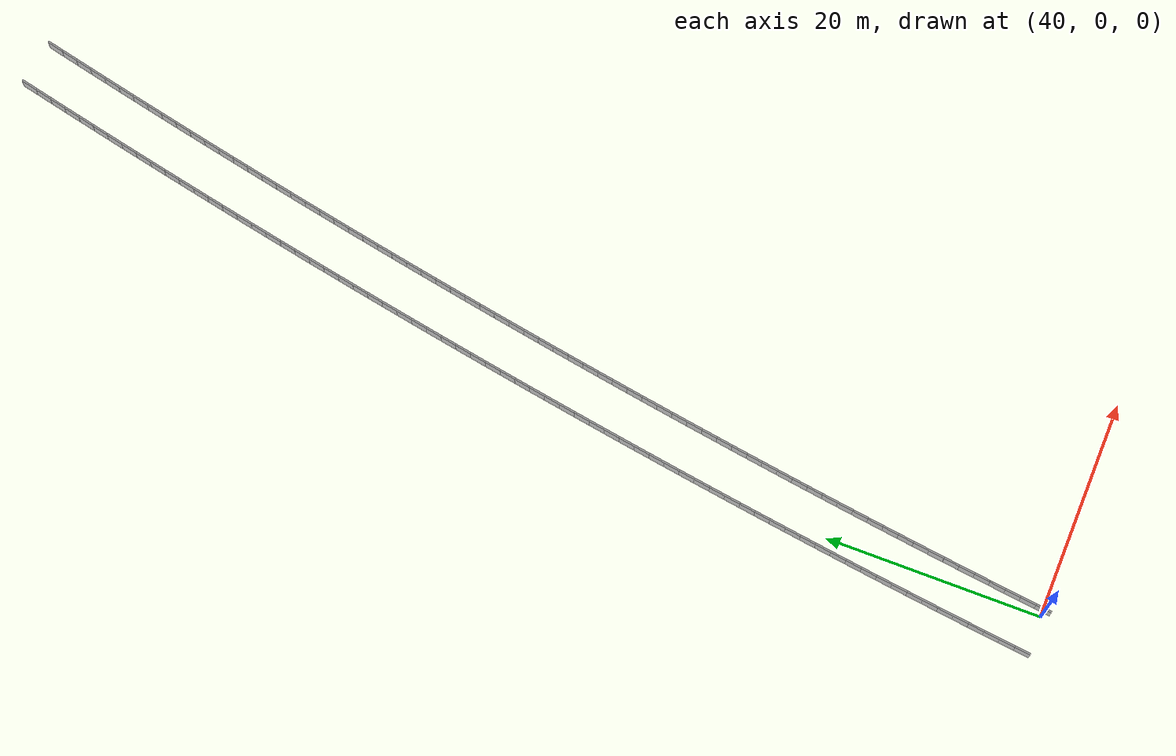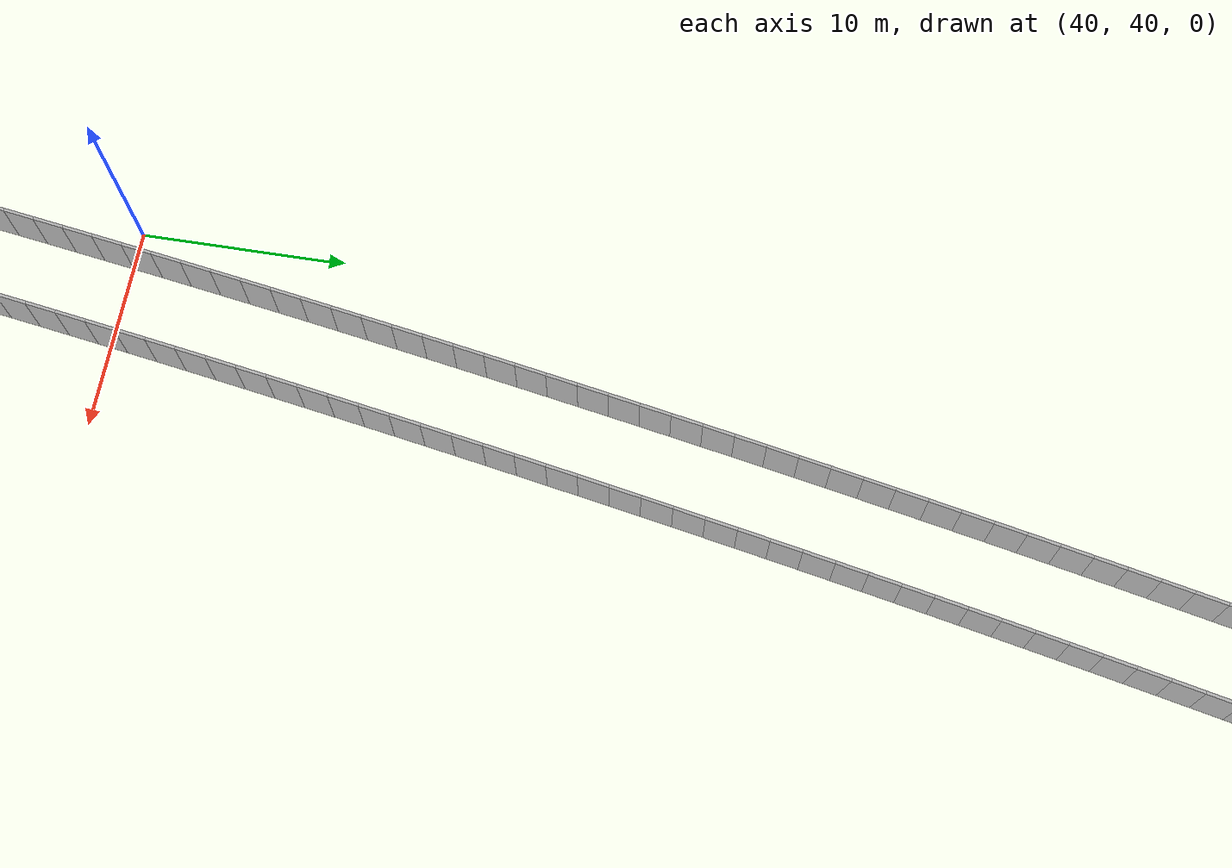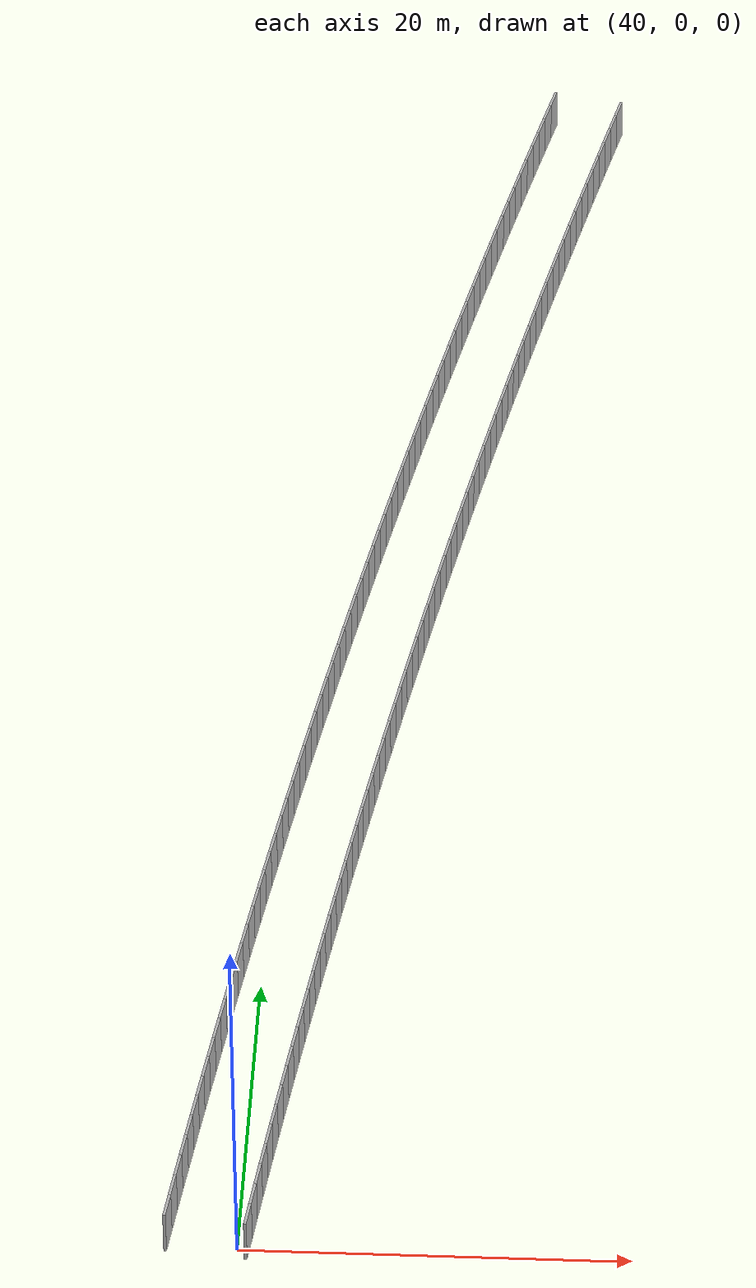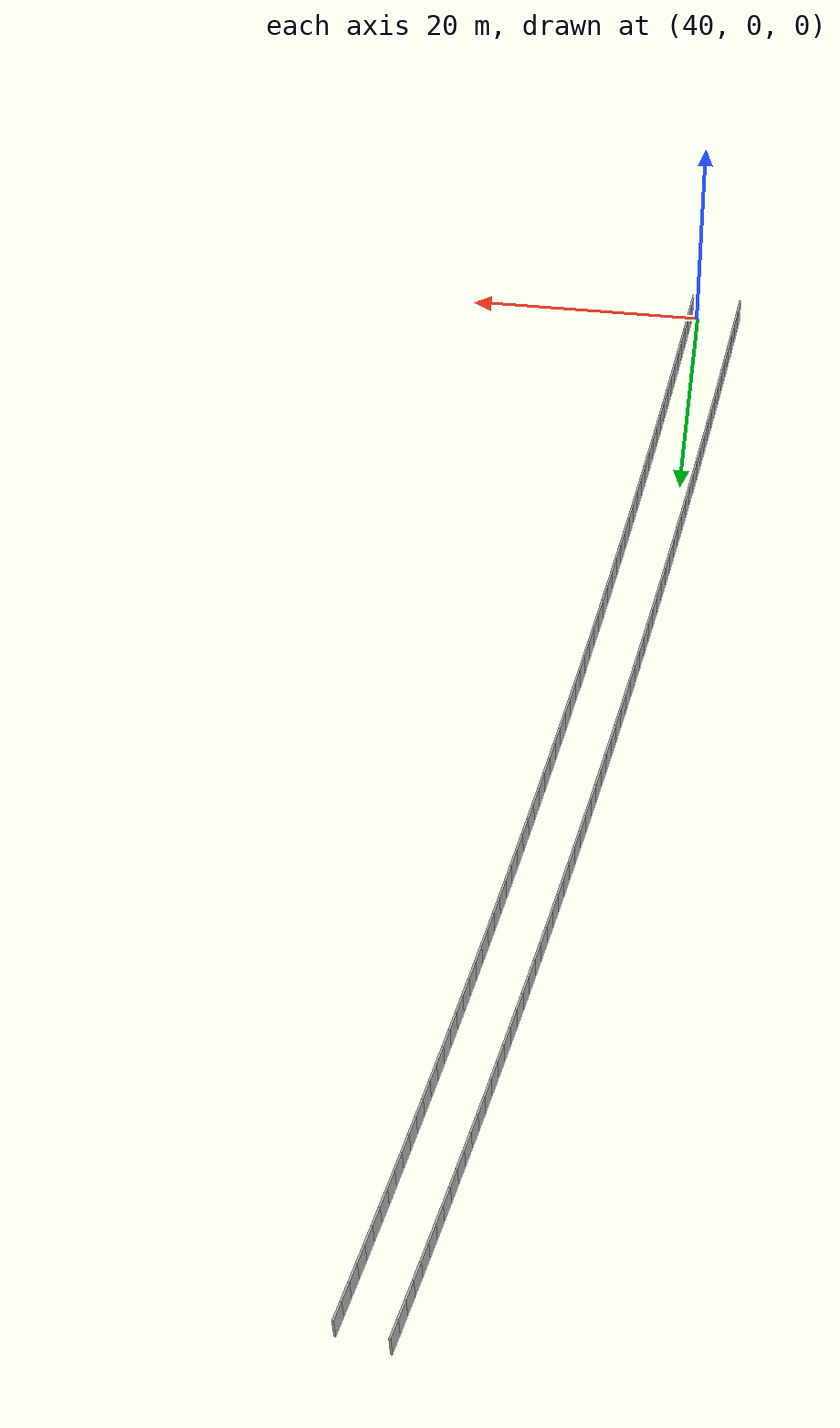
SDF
<?xml version="1.0" ?>
<sdf version="1.6">
  <model name="sps_0114">
    <pose frame="">0 0 0 0 -0 0</pose>
    <static>1</static>
    <self_collide>0</self_collide>
    <allow_auto_disable>0</allow_auto_disable>
    <link name="Wall5109">
      <kinematic>0</kinematic>
      <gravity>1</gravity>
      <self_collide>0</self_collide>
      <collision name="collision">
        <geometry>
          <box>
            <size>1.4965 0.15 2.5</size>
          </box>
        </geometry>
        <pose frame="">0 0 0 0 -0 0</pose>
      </collision>
      <visual name="visual">
        <geometry>
          <box>
            <size>1.4965 0.15 2.5</size>
          </box>
        </geometry>
        <pose frame="">0 0 0 0 -0 0</pose>
        <cast_shadows>1</cast_shadows>
        <transparency>0.0</transparency>
      </visual>
      <pose frame="">57.1898 98.9115 1.25 0 0 -1.79093</pose>
    </link>
    <link name="Wall5110">
      <kinematic>0</kinematic>
      <gravity>1</gravity>
      <self_collide>0</self_collide>
      <collision name="collision">
        <geometry>
          <box>
            <size>1.49658 0.15 2.5</size>
          </box>
        </geometry>
        <pose frame="">0 0 0 0 -0 0</pose>
      </collision>
      <visual name="visual">
        <geometry>
          <box>
            <size>1.49658 0.15 2.5</size>
          </box>
        </geometry>
        <pose frame="">0 0 0 0 -0 0</pose>
        <cast_shadows>1</cast_shadows>
        <transparency>0.0</transparency>
      </visual>
      <pose frame="">56.8642 97.4508 1.25 0 0 -1.78929</pose>
    </link>
    <link name="Wall5111">
      <kinematic>0</kinematic>
      <gravity>1</gravity>
      <self_collide>0</self_collide>
      <collision name="collision">
        <geometry>
          <box>
            <size>1.49648 0.15 2.5</size>
          </box>
        </geometry>
        <pose frame="">0 0 0 0 -0 0</pose>
      </collision>
      <visual name="visual">
        <geometry>
          <box>
            <size>1.49648 0.15 2.5</size>
          </box>
        </geometry>
        <pose frame="">0 0 0 0 -0 0</pose>
        <cast_shadows>1</cast_shadows>
        <transparency>0.0</transparency>
      </visual>
      <pose frame="">56.541 95.9896 1.25 0 0 -1.78768</pose>
    </link>
    <link name="Wall5112">
      <kinematic>0</kinematic>
      <gravity>1</gravity>
      <self_collide>0</self_collide>
      <collision name="collision">
        <geometry>
          <box>
            <size>1.49654 0.15 2.5</size>
          </box>
        </geometry>
        <pose frame="">0 0 0 0 -0 0</pose>
      </collision>
      <visual name="visual">
        <geometry>
          <box>
            <size>1.49654 0.15 2.5</size>
          </box>
        </geometry>
        <pose frame="">0 0 0 0 -0 0</pose>
        <cast_shadows>1</cast_shadows>
        <transparency>0.0</transparency>
      </visual>
      <pose frame="">56.2201 94.5279 1.25 0 0 -1.78613</pose>
    </link>
    <link name="Wall5113">
      <kinematic>0</kinematic>
      <gravity>1</gravity>
      <self_collide>0</self_collide>
      <collision name="collision">
        <geometry>
          <box>
            <size>1.4965 0.15 2.5</size>
          </box>
        </geometry>
        <pose frame="">0 0 0 0 -0 0</pose>
      </collision>
      <visual name="visual">
        <geometry>
          <box>
            <size>1.4965 0.15 2.5</size>
          </box>
        </geometry>
        <pose frame="">0 0 0 0 -0 0</pose>
        <cast_shadows>1</cast_shadows>
        <transparency>0.0</transparency>
      </visual>
      <pose frame="">55.9015 93.0657 1.25 0 0 -1.78467</pose>
    </link>
    <link name="Wall5114">
      <kinematic>0</kinematic>
      <gravity>1</gravity>
      <self_collide>0</self_collide>
      <collision name="collision">
        <geometry>
          <box>
            <size>1.49654 0.15 2.5</size>
          </box>
        </geometry>
        <pose frame="">0 0 0 0 -0 0</pose>
      </collision>
      <visual name="visual">
        <geometry>
          <box>
            <size>1.49654 0.15 2.5</size>
          </box>
        </geometry>
        <pose frame="">0 0 0 0 -0 0</pose>
        <cast_shadows>1</cast_shadows>
        <transparency>0.0</transparency>
      </visual>
      <pose frame="">55.5851 91.603 1.25 0 0 -1.78287</pose>
    </link>
    <link name="Wall5115">
      <kinematic>0</kinematic>
      <gravity>1</gravity>
      <self_collide>0</self_collide>
      <collision name="collision">
        <geometry>
          <box>
            <size>1.49639 0.15 2.5</size>
          </box>
        </geometry>
        <pose frame="">0 0 0 0 -0 0</pose>
      </collision>
      <visual name="visual">
        <geometry>
          <box>
            <size>1.49639 0.15 2.5</size>
          </box>
        </geometry>
        <pose frame="">0 0 0 0 -0 0</pose>
        <cast_shadows>1</cast_shadows>
        <transparency>0.0</transparency>
      </visual>
      <pose frame="">55.2714 90.1398 1.25 0 0 -1.78122</pose>
    </link>
    <link name="Wall5116">
      <kinematic>0</kinematic>
      <gravity>1</gravity>
      <self_collide>0</self_collide>
      <collision name="collision">
        <geometry>
          <box>
            <size>1.49654 0.15 2.5</size>
          </box>
        </geometry>
        <pose frame="">0 0 0 0 -0 0</pose>
      </collision>
      <visual name="visual">
        <geometry>
          <box>
            <size>1.49654 0.15 2.5</size>
          </box>
        </geometry>
        <pose frame="">0 0 0 0 -0 0</pose>
        <cast_shadows>1</cast_shadows>
        <transparency>0.0</transparency>
      </visual>
      <pose frame="">54.9599 88.6761 1.25 0 0 -1.77974</pose>
    </link>
    <link name="Wall5117">
      <kinematic>0</kinematic>
      <gravity>1</gravity>
      <self_collide>0</self_collide>
      <collision name="collision">
        <geometry>
          <box>
            <size>1.49649 0.15 2.5</size>
          </box>
        </geometry>
        <pose frame="">0 0 0 0 -0 0</pose>
      </collision>
      <visual name="visual">
        <geometry>
          <box>
            <size>1.49649 0.15 2.5</size>
          </box>
        </geometry>
        <pose frame="">0 0 0 0 -0 0</pose>
        <cast_shadows>1</cast_shadows>
        <transparency>0.0</transparency>
      </visual>
      <pose frame="">54.6506 87.2119 1.25 0 0 -1.77821</pose>
    </link>
    <link name="Wall5118">
      <kinematic>0</kinematic>
      <gravity>1</gravity>
      <self_collide>0</self_collide>
      <collision name="collision">
        <geometry>
          <box>
            <size>1.49637 0.15 2.5</size>
          </box>
        </geometry>
        <pose frame="">0 0 0 0 -0 0</pose>
      </collision>
      <visual name="visual">
        <geometry>
          <box>
            <size>1.49637 0.15 2.5</size>
          </box>
        </geometry>
        <pose frame="">0 0 0 0 -0 0</pose>
        <cast_shadows>1</cast_shadows>
        <transparency>0.0</transparency>
      </visual>
      <pose frame="">54.3436 85.7473 1.25 0 0 -1.77664</pose>
    </link>
    <link name="Wall5119">
      <kinematic>0</kinematic>
      <gravity>1</gravity>
      <self_collide>0</self_collide>
      <collision name="collision">
        <geometry>
          <box>
            <size>1.49675 0.15 2.5</size>
          </box>
        </geometry>
        <pose frame="">0 0 0 0 -0 0</pose>
      </collision>
      <visual name="visual">
        <geometry>
          <box>
            <size>1.49675 0.15 2.5</size>
          </box>
        </geometry>
        <pose frame="">0 0 0 0 -0 0</pose>
        <cast_shadows>1</cast_shadows>
        <transparency>0.0</transparency>
      </visual>
      <pose frame="">54.0388 84.2821 1.25 0 0 -1.77505</pose>
    </link>
    <link name="Wall5120">
      <kinematic>0</kinematic>
      <gravity>1</gravity>
      <self_collide>0</self_collide>
      <collision name="collision">
        <geometry>
          <box>
            <size>1.49639 0.15 2.5</size>
          </box>
        </geometry>
        <pose frame="">0 0 0 0 -0 0</pose>
      </collision>
      <visual name="visual">
        <geometry>
          <box>
            <size>1.49639 0.15 2.5</size>
          </box>
        </geometry>
        <pose frame="">0 0 0 0 -0 0</pose>
        <cast_shadows>1</cast_shadows>
        <transparency>0.0</transparency>
      </visual>
      <pose frame="">53.7364 82.8164 1.25 0 0 -1.77347</pose>
    </link>
    <link name="Wall5121">
      <kinematic>0</kinematic>
      <gravity>1</gravity>
      <self_collide>0</self_collide>
      <collision name="collision">
        <geometry>
          <box>
            <size>1.49656 0.15 2.5</size>
          </box>
        </geometry>
        <pose frame="">0 0 0 0 -0 0</pose>
      </collision>
      <visual name="visual">
        <geometry>
          <box>
            <size>1.49656 0.15 2.5</size>
          </box>
        </geometry>
        <pose frame="">0 0 0 0 -0 0</pose>
        <cast_shadows>1</cast_shadows>
        <transparency>0.0</transparency>
      </visual>
      <pose frame="">53.4365 81.3503 1.25 0 0 -1.77178</pose>
    </link>
    <link name="Wall5122">
      <kinematic>0</kinematic>
      <gravity>1</gravity>
      <self_collide>0</self_collide>
      <collision name="collision">
        <geometry>
          <box>
            <size>1.49649 0.15 2.5</size>
          </box>
        </geometry>
        <pose frame="">0 0 0 0 -0 0</pose>
      </collision>
      <visual name="visual">
        <geometry>
          <box>
            <size>1.49649 0.15 2.5</size>
          </box>
        </geometry>
        <pose frame="">0 0 0 0 -0 0</pose>
        <cast_shadows>1</cast_shadows>
        <transparency>0.0</transparency>
      </visual>
      <pose frame="">53.1388 79.8837 1.25 0 0 -1.77034</pose>
    </link>
    <link name="Wall5123">
      <kinematic>0</kinematic>
      <gravity>1</gravity>
      <self_collide>0</self_collide>
      <collision name="collision">
        <geometry>
          <box>
            <size>1.49661 0.15 2.5</size>
          </box>
        </geometry>
        <pose frame="">0 0 0 0 -0 0</pose>
      </collision>
      <visual name="visual">
        <geometry>
          <box>
            <size>1.49661 0.15 2.5</size>
          </box>
        </geometry>
        <pose frame="">0 0 0 0 -0 0</pose>
        <cast_shadows>1</cast_shadows>
        <transparency>0.0</transparency>
      </visual>
      <pose frame="">52.8433 78.4166 1.25 0 0 -1.76866</pose>
    </link>
    <link name="Wall5124">
      <kinematic>0</kinematic>
      <gravity>1</gravity>
      <self_collide>0</self_collide>
      <collision name="collision">
        <geometry>
          <box>
            <size>1.4965 0.15 2.5</size>
          </box>
        </geometry>
        <pose frame="">0 0 0 0 -0 0</pose>
      </collision>
      <visual name="visual">
        <geometry>
          <box>
            <size>1.4965 0.15 2.5</size>
          </box>
        </geometry>
        <pose frame="">0 0 0 0 -0 0</pose>
        <cast_shadows>1</cast_shadows>
        <transparency>0.0</transparency>
      </visual>
      <pose frame="">52.5503 76.949 1.25 0 0 -1.76705</pose>
    </link>
    <link name="Wall5125">
      <kinematic>0</kinematic>
      <gravity>1</gravity>
      <self_collide>0</self_collide>
      <collision name="collision">
        <geometry>
          <box>
            <size>1.49649 0.15 2.5</size>
          </box>
        </geometry>
        <pose frame="">0 0 0 0 -0 0</pose>
      </collision>
      <visual name="visual">
        <geometry>
          <box>
            <size>1.49649 0.15 2.5</size>
          </box>
        </geometry>
        <pose frame="">0 0 0 0 -0 0</pose>
        <cast_shadows>1</cast_shadows>
        <transparency>0.0</transparency>
      </visual>
      <pose frame="">52.2596 75.481 1.25 0 0 -1.76555</pose>
    </link>
    <link name="Wall5126">
      <kinematic>0</kinematic>
      <gravity>1</gravity>
      <self_collide>0</self_collide>
      <collision name="collision">
        <geometry>
          <box>
            <size>1.49662 0.15 2.5</size>
          </box>
        </geometry>
        <pose frame="">0 0 0 0 -0 0</pose>
      </collision>
      <visual name="visual">
        <geometry>
          <box>
            <size>1.49662 0.15 2.5</size>
          </box>
        </geometry>
        <pose frame="">0 0 0 0 -0 0</pose>
        <cast_shadows>1</cast_shadows>
        <transparency>0.0</transparency>
      </visual>
      <pose frame="">51.9712 74.0125 1.25 0 0 -1.76387</pose>
    </link>
    <link name="Wall5127">
      <kinematic>0</kinematic>
      <gravity>1</gravity>
      <self_collide>0</self_collide>
      <collision name="collision">
        <geometry>
          <box>
            <size>1.49635 0.15 2.5</size>
          </box>
        </geometry>
        <pose frame="">0 0 0 0 -0 0</pose>
      </collision>
      <visual name="visual">
        <geometry>
          <box>
            <size>1.49635 0.15 2.5</size>
          </box>
        </geometry>
        <pose frame="">0 0 0 0 -0 0</pose>
        <cast_shadows>1</cast_shadows>
        <transparency>0.0</transparency>
      </visual>
      <pose frame="">51.6853 72.5436 1.25 0 0 -1.76229</pose>
    </link>
    <link name="Wall5128">
      <kinematic>0</kinematic>
      <gravity>1</gravity>
      <self_collide>0</self_collide>
      <collision name="collision">
        <geometry>
          <box>
            <size>1.49653 0.15 2.5</size>
          </box>
        </geometry>
        <pose frame="">0 0 0 0 -0 0</pose>
      </collision>
      <visual name="visual">
        <geometry>
          <box>
            <size>1.49653 0.15 2.5</size>
          </box>
        </geometry>
        <pose frame="">0 0 0 0 -0 0</pose>
        <cast_shadows>1</cast_shadows>
        <transparency>0.0</transparency>
      </visual>
      <pose frame="">51.4016 71.0743 1.25 0 0 -1.76077</pose>
    </link>
    <link name="Wall5129">
      <kinematic>0</kinematic>
      <gravity>1</gravity>
      <self_collide>0</self_collide>
      <collision name="collision">
        <geometry>
          <box>
            <size>1.49668 0.15 2.5</size>
          </box>
        </geometry>
        <pose frame="">0 0 0 0 -0 0</pose>
      </collision>
      <visual name="visual">
        <geometry>
          <box>
            <size>1.49668 0.15 2.5</size>
          </box>
        </geometry>
        <pose frame="">0 0 0 0 -0 0</pose>
        <cast_shadows>1</cast_shadows>
        <transparency>0.0</transparency>
      </visual>
      <pose frame="">51.1202 69.6044 1.25 0 0 -1.75913</pose>
    </link>
    <link name="Wall5130">
      <kinematic>0</kinematic>
      <gravity>1</gravity>
      <self_collide>0</self_collide>
      <collision name="collision">
        <geometry>
          <box>
            <size>1.49645 0.15 2.5</size>
          </box>
        </geometry>
        <pose frame="">0 0 0 0 -0 0</pose>
      </collision>
      <visual name="visual">
        <geometry>
          <box>
            <size>1.49645 0.15 2.5</size>
          </box>
        </geometry>
        <pose frame="">0 0 0 0 -0 0</pose>
        <cast_shadows>1</cast_shadows>
        <transparency>0.0</transparency>
      </visual>
      <pose frame="">50.8411 68.1341 1.25 0 0 -1.75767</pose>
    </link>
    <link name="Wall5131">
      <kinematic>0</kinematic>
      <gravity>1</gravity>
      <self_collide>0</self_collide>
      <collision name="collision">
        <geometry>
          <box>
            <size>1.4966 0.15 2.5</size>
          </box>
        </geometry>
        <pose frame="">0 0 0 0 -0 0</pose>
      </collision>
      <visual name="visual">
        <geometry>
          <box>
            <size>1.4966 0.15 2.5</size>
          </box>
        </geometry>
        <pose frame="">0 0 0 0 -0 0</pose>
        <cast_shadows>1</cast_shadows>
        <transparency>0.0</transparency>
      </visual>
      <pose frame="">50.5643 66.6634 1.25 0 0 -1.75599</pose>
    </link>
    <link name="Wall5132">
      <kinematic>0</kinematic>
      <gravity>1</gravity>
      <self_collide>0</self_collide>
      <collision name="collision">
        <geometry>
          <box>
            <size>1.49634 0.15 2.5</size>
          </box>
        </geometry>
        <pose frame="">0 0 0 0 -0 0</pose>
      </collision>
      <visual name="visual">
        <geometry>
          <box>
            <size>1.49634 0.15 2.5</size>
          </box>
        </geometry>
        <pose frame="">0 0 0 0 -0 0</pose>
        <cast_shadows>1</cast_shadows>
        <transparency>0.0</transparency>
      </visual>
      <pose frame="">50.2899 65.1923 1.25 0 0 -1.7544</pose>
    </link>
    <link name="Wall5133">
      <kinematic>0</kinematic>
      <gravity>1</gravity>
      <self_collide>0</self_collide>
      <collision name="collision">
        <geometry>
          <box>
            <size>1.49654 0.15 2.5</size>
          </box>
        </geometry>
        <pose frame="">0 0 0 0 -0 0</pose>
      </collision>
      <visual name="visual">
        <geometry>
          <box>
            <size>1.49654 0.15 2.5</size>
          </box>
        </geometry>
        <pose frame="">0 0 0 0 -0 0</pose>
        <cast_shadows>1</cast_shadows>
        <transparency>0.0</transparency>
      </visual>
      <pose frame="">50.0178 63.7208 1.25 0 0 -1.75288</pose>
    </link>
    <link name="Wall5134">
      <kinematic>0</kinematic>
      <gravity>1</gravity>
      <self_collide>0</self_collide>
      <collision name="collision">
        <geometry>
          <box>
            <size>1.49668 0.15 2.5</size>
          </box>
        </geometry>
        <pose frame="">0 0 0 0 -0 0</pose>
      </collision>
      <visual name="visual">
        <geometry>
          <box>
            <size>1.49668 0.15 2.5</size>
          </box>
        </geometry>
        <pose frame="">0 0 0 0 -0 0</pose>
        <cast_shadows>1</cast_shadows>
        <transparency>0.0</transparency>
      </visual>
      <pose frame="">49.7481 62.2487 1.25 0 0 -1.75112</pose>
    </link>
    <link name="Wall5135">
      <kinematic>0</kinematic>
      <gravity>1</gravity>
      <self_collide>0</self_collide>
      <collision name="collision">
        <geometry>
          <box>
            <size>1.4965 0.15 2.5</size>
          </box>
        </geometry>
        <pose frame="">0 0 0 0 -0 0</pose>
      </collision>
      <visual name="visual">
        <geometry>
          <box>
            <size>1.4965 0.15 2.5</size>
          </box>
        </geometry>
        <pose frame="">0 0 0 0 -0 0</pose>
        <cast_shadows>1</cast_shadows>
        <transparency>0.0</transparency>
      </visual>
      <pose frame="">49.4806 60.7762 1.25 0 0 -1.74978</pose>
    </link>
    <link name="Wall5136">
      <kinematic>0</kinematic>
      <gravity>1</gravity>
      <self_collide>0</self_collide>
      <collision name="collision">
        <geometry>
          <box>
            <size>1.4964 0.15 2.5</size>
          </box>
        </geometry>
        <pose frame="">0 0 0 0 -0 0</pose>
      </collision>
      <visual name="visual">
        <geometry>
          <box>
            <size>1.4964 0.15 2.5</size>
          </box>
        </geometry>
        <pose frame="">0 0 0 0 -0 0</pose>
        <cast_shadows>1</cast_shadows>
        <transparency>0.0</transparency>
      </visual>
      <pose frame="">49.2155 59.3034 1.25 0 0 -1.74801</pose>
    </link>
    <link name="Wall5137">
      <kinematic>0</kinematic>
      <gravity>1</gravity>
      <self_collide>0</self_collide>
      <collision name="collision">
        <geometry>
          <box>
            <size>1.49667 0.15 2.5</size>
          </box>
        </geometry>
        <pose frame="">0 0 0 0 -0 0</pose>
      </collision>
      <visual name="visual">
        <geometry>
          <box>
            <size>1.49667 0.15 2.5</size>
          </box>
        </geometry>
        <pose frame="">0 0 0 0 -0 0</pose>
        <cast_shadows>1</cast_shadows>
        <transparency>0.0</transparency>
      </visual>
      <pose frame="">48.9528 57.8301 1.25 0 0 -1.74648</pose>
    </link>
    <link name="Wall5138">
      <kinematic>0</kinematic>
      <gravity>1</gravity>
      <self_collide>0</self_collide>
      <collision name="collision">
        <geometry>
          <box>
            <size>1.49641 0.15 2.5</size>
          </box>
        </geometry>
        <pose frame="">0 0 0 0 -0 0</pose>
      </collision>
      <visual name="visual">
        <geometry>
          <box>
            <size>1.49641 0.15 2.5</size>
          </box>
        </geometry>
        <pose frame="">0 0 0 0 -0 0</pose>
        <cast_shadows>1</cast_shadows>
        <transparency>0.0</transparency>
      </visual>
      <pose frame="">48.6923 56.3564 1.25 0 0 -1.74502</pose>
    </link>
    <link name="Wall5139">
      <kinematic>0</kinematic>
      <gravity>1</gravity>
      <self_collide>0</self_collide>
      <collision name="collision">
        <geometry>
          <box>
            <size>1.49662 0.15 2.5</size>
          </box>
        </geometry>
        <pose frame="">0 0 0 0 -0 0</pose>
      </collision>
      <visual name="visual">
        <geometry>
          <box>
            <size>1.49662 0.15 2.5</size>
          </box>
        </geometry>
        <pose frame="">0 0 0 0 -0 0</pose>
        <cast_shadows>1</cast_shadows>
        <transparency>0.0</transparency>
      </visual>
      <pose frame="">48.4343 54.8823 1.25 0 0 -1.74322</pose>
    </link>
    <link name="Wall5140">
      <kinematic>0</kinematic>
      <gravity>1</gravity>
      <self_collide>0</self_collide>
      <collision name="collision">
        <geometry>
          <box>
            <size>1.49643 0.15 2.5</size>
          </box>
        </geometry>
        <pose frame="">0 0 0 0 -0 0</pose>
      </collision>
      <visual name="visual">
        <geometry>
          <box>
            <size>1.49643 0.15 2.5</size>
          </box>
        </geometry>
        <pose frame="">0 0 0 0 -0 0</pose>
        <cast_shadows>1</cast_shadows>
        <transparency>0.0</transparency>
      </visual>
      <pose frame="">48.1786 53.4078 1.25 0 0 -1.74179</pose>
    </link>
    <link name="Wall5141">
      <kinematic>0</kinematic>
      <gravity>1</gravity>
      <self_collide>0</self_collide>
      <collision name="collision">
        <geometry>
          <box>
            <size>1.49662 0.15 2.5</size>
          </box>
        </geometry>
        <pose frame="">0 0 0 0 -0 0</pose>
      </collision>
      <visual name="visual">
        <geometry>
          <box>
            <size>1.49662 0.15 2.5</size>
          </box>
        </geometry>
        <pose frame="">0 0 0 0 -0 0</pose>
        <cast_shadows>1</cast_shadows>
        <transparency>0.0</transparency>
      </visual>
      <pose frame="">47.9251 51.9329 1.25 0 0 -1.74012</pose>
    </link>
    <link name="Wall5142">
      <kinematic>0</kinematic>
      <gravity>1</gravity>
      <self_collide>0</self_collide>
      <collision name="collision">
        <geometry>
          <box>
            <size>1.49643 0.15 2.5</size>
          </box>
        </geometry>
        <pose frame="">0 0 0 0 -0 0</pose>
      </collision>
      <visual name="visual">
        <geometry>
          <box>
            <size>1.49643 0.15 2.5</size>
          </box>
        </geometry>
        <pose frame="">0 0 0 0 -0 0</pose>
        <cast_shadows>1</cast_shadows>
        <transparency>0.0</transparency>
      </visual>
      <pose frame="">47.674 50.4576 1.25 0 0 -1.73865</pose>
    </link>
    <link name="Wall5143">
      <kinematic>0</kinematic>
      <gravity>1</gravity>
      <self_collide>0</self_collide>
      <collision name="collision">
        <geometry>
          <box>
            <size>1.49657 0.15 2.5</size>
          </box>
        </geometry>
        <pose frame="">0 0 0 0 -0 0</pose>
      </collision>
      <visual name="visual">
        <geometry>
          <box>
            <size>1.49657 0.15 2.5</size>
          </box>
        </geometry>
        <pose frame="">0 0 0 0 -0 0</pose>
        <cast_shadows>1</cast_shadows>
        <transparency>0.0</transparency>
      </visual>
      <pose frame="">47.4253 48.9819 1.25 0 0 -1.73698</pose>
    </link>
    <link name="Wall5144">
      <kinematic>0</kinematic>
      <gravity>1</gravity>
      <self_collide>0</self_collide>
      <collision name="collision">
        <geometry>
          <box>
            <size>1.49643 0.15 2.5</size>
          </box>
        </geometry>
        <pose frame="">0 0 0 0 -0 0</pose>
      </collision>
      <visual name="visual">
        <geometry>
          <box>
            <size>1.49643 0.15 2.5</size>
          </box>
        </geometry>
        <pose frame="">0 0 0 0 -0 0</pose>
        <cast_shadows>1</cast_shadows>
        <transparency>0.0</transparency>
      </visual>
      <pose frame="">47.1789 47.5058 1.25 0 0 -1.73542</pose>
    </link>
    <link name="Wall5145">
      <kinematic>0</kinematic>
      <gravity>1</gravity>
      <self_collide>0</self_collide>
      <collision name="collision">
        <geometry>
          <box>
            <size>1.49645 0.15 2.5</size>
          </box>
        </geometry>
        <pose frame="">0 0 0 0 -0 0</pose>
      </collision>
      <visual name="visual">
        <geometry>
          <box>
            <size>1.49645 0.15 2.5</size>
          </box>
        </geometry>
        <pose frame="">0 0 0 0 -0 0</pose>
        <cast_shadows>1</cast_shadows>
        <transparency>0.0</transparency>
      </visual>
      <pose frame="">46.9348 46.0294 1.25 0 0 -1.73377</pose>
    </link>
    <link name="Wall5146">
      <kinematic>0</kinematic>
      <gravity>1</gravity>
      <self_collide>0</self_collide>
      <collision name="collision">
        <geometry>
          <box>
            <size>1.49664 0.15 2.5</size>
          </box>
        </geometry>
        <pose frame="">0 0 0 0 -0 0</pose>
      </collision>
      <visual name="visual">
        <geometry>
          <box>
            <size>1.49664 0.15 2.5</size>
          </box>
        </geometry>
        <pose frame="">0 0 0 0 -0 0</pose>
        <cast_shadows>1</cast_shadows>
        <transparency>0.0</transparency>
      </visual>
      <pose frame="">46.6931 44.5525 1.25 0 0 -1.73226</pose>
    </link>
    <link name="Wall5147">
      <kinematic>0</kinematic>
      <gravity>1</gravity>
      <self_collide>0</self_collide>
      <collision name="collision">
        <geometry>
          <box>
            <size>1.49649 0.15 2.5</size>
          </box>
        </geometry>
        <pose frame="">0 0 0 0 -0 0</pose>
      </collision>
      <visual name="visual">
        <geometry>
          <box>
            <size>1.49649 0.15 2.5</size>
          </box>
        </geometry>
        <pose frame="">0 0 0 0 -0 0</pose>
        <cast_shadows>1</cast_shadows>
        <transparency>0.0</transparency>
      </visual>
      <pose frame="">46.4538 43.0752 1.25 0 0 -1.73062</pose>
    </link>
    <link name="Wall5148">
      <kinematic>0</kinematic>
      <gravity>1</gravity>
      <self_collide>0</self_collide>
      <collision name="collision">
        <geometry>
          <box>
            <size>1.49651 0.15 2.5</size>
          </box>
        </geometry>
        <pose frame="">0 0 0 0 -0 0</pose>
      </collision>
      <visual name="visual">
        <geometry>
          <box>
            <size>1.49651 0.15 2.5</size>
          </box>
        </geometry>
        <pose frame="">0 0 0 0 -0 0</pose>
        <cast_shadows>1</cast_shadows>
        <transparency>0.0</transparency>
      </visual>
      <pose frame="">46.2167 41.5976 1.25 0 0 -1.72917</pose>
    </link>
    <link name="Wall5149">
      <kinematic>0</kinematic>
      <gravity>1</gravity>
      <self_collide>0</self_collide>
      <collision name="collision">
        <geometry>
          <box>
            <size>1.49652 0.15 2.5</size>
          </box>
        </geometry>
        <pose frame="">0 0 0 0 -0 0</pose>
      </collision>
      <visual name="visual">
        <geometry>
          <box>
            <size>1.49652 0.15 2.5</size>
          </box>
        </geometry>
        <pose frame="">0 0 0 0 -0 0</pose>
        <cast_shadows>1</cast_shadows>
        <transparency>0.0</transparency>
      </visual>
      <pose frame="">45.982 40.1196 1.25 0 0 -1.7274</pose>
    </link>
    <link name="Wall5150">
      <kinematic>0</kinematic>
      <gravity>1</gravity>
      <self_collide>0</self_collide>
      <collision name="collision">
        <geometry>
          <box>
            <size>1.4966 0.15 2.5</size>
          </box>
        </geometry>
        <pose frame="">0 0 0 0 -0 0</pose>
      </collision>
      <visual name="visual">
        <geometry>
          <box>
            <size>1.4966 0.15 2.5</size>
          </box>
        </geometry>
        <pose frame="">0 0 0 0 -0 0</pose>
        <cast_shadows>1</cast_shadows>
        <transparency>0.0</transparency>
      </visual>
      <pose frame="">45.7497 38.6412 1.25 0 0 -1.7259</pose>
    </link>
    <link name="Wall5151">
      <kinematic>0</kinematic>
      <gravity>1</gravity>
      <self_collide>0</self_collide>
      <collision name="collision">
        <geometry>
          <box>
            <size>1.49639 0.15 2.5</size>
          </box>
        </geometry>
        <pose frame="">0 0 0 0 -0 0</pose>
      </collision>
      <visual name="visual">
        <geometry>
          <box>
            <size>1.49639 0.15 2.5</size>
          </box>
        </geometry>
        <pose frame="">0 0 0 0 -0 0</pose>
        <cast_shadows>1</cast_shadows>
        <transparency>0.0</transparency>
      </visual>
      <pose frame="">45.5196 37.1625 1.25 0 0 -1.72444</pose>
    </link>
    <link name="Wall5152">
      <kinematic>0</kinematic>
      <gravity>1</gravity>
      <self_collide>0</self_collide>
      <collision name="collision">
        <geometry>
          <box>
            <size>1.49665 0.15 2.5</size>
          </box>
        </geometry>
        <pose frame="">0 0 0 0 -0 0</pose>
      </collision>
      <visual name="visual">
        <geometry>
          <box>
            <size>1.49665 0.15 2.5</size>
          </box>
        </geometry>
        <pose frame="">0 0 0 0 -0 0</pose>
        <cast_shadows>1</cast_shadows>
        <transparency>0.0</transparency>
      </visual>
      <pose frame="">45.2919 35.6834 1.25 0 0 -1.72264</pose>
    </link>
    <link name="Wall5153">
      <kinematic>0</kinematic>
      <gravity>1</gravity>
      <self_collide>0</self_collide>
      <collision name="collision">
        <geometry>
          <box>
            <size>1.49651 0.15 2.5</size>
          </box>
        </geometry>
        <pose frame="">0 0 0 0 -0 0</pose>
      </collision>
      <visual name="visual">
        <geometry>
          <box>
            <size>1.49651 0.15 2.5</size>
          </box>
        </geometry>
        <pose frame="">0 0 0 0 -0 0</pose>
        <cast_shadows>1</cast_shadows>
        <transparency>0.0</transparency>
      </visual>
      <pose frame="">45.0666 34.2039 1.25 0 0 -1.72121</pose>
    </link>
    <link name="Wall5154">
      <kinematic>0</kinematic>
      <gravity>1</gravity>
      <self_collide>0</self_collide>
      <collision name="collision">
        <geometry>
          <box>
            <size>1.49651 0.15 2.5</size>
          </box>
        </geometry>
        <pose frame="">0 0 0 0 -0 0</pose>
      </collision>
      <visual name="visual">
        <geometry>
          <box>
            <size>1.49651 0.15 2.5</size>
          </box>
        </geometry>
        <pose frame="">0 0 0 0 -0 0</pose>
        <cast_shadows>1</cast_shadows>
        <transparency>0.0</transparency>
      </visual>
      <pose frame="">44.8435 32.7241 1.25 0 0 -1.71956</pose>
    </link>
    <link name="Wall5155">
      <kinematic>0</kinematic>
      <gravity>1</gravity>
      <self_collide>0</self_collide>
      <collision name="collision">
        <geometry>
          <box>
            <size>1.49657 0.15 2.5</size>
          </box>
        </geometry>
        <pose frame="">0 0 0 0 -0 0</pose>
      </collision>
      <visual name="visual">
        <geometry>
          <box>
            <size>1.49657 0.15 2.5</size>
          </box>
        </geometry>
        <pose frame="">0 0 0 0 -0 0</pose>
        <cast_shadows>1</cast_shadows>
        <transparency>0.0</transparency>
      </visual>
      <pose frame="">44.6229 31.2439 1.25 0 0 -1.7179</pose>
    </link>
    <link name="Wall5156">
      <kinematic>0</kinematic>
      <gravity>1</gravity>
      <self_collide>0</self_collide>
      <collision name="collision">
        <geometry>
          <box>
            <size>1.49644 0.15 2.5</size>
          </box>
        </geometry>
        <pose frame="">0 0 0 0 -0 0</pose>
      </collision>
      <visual name="visual">
        <geometry>
          <box>
            <size>1.49644 0.15 2.5</size>
          </box>
        </geometry>
        <pose frame="">0 0 0 0 -0 0</pose>
        <cast_shadows>1</cast_shadows>
        <transparency>0.0</transparency>
      </visual>
      <pose frame="">44.4047 29.7634 1.25 0 0 -1.71647</pose>
    </link>
    <link name="Wall5157">
      <kinematic>0</kinematic>
      <gravity>1</gravity>
      <self_collide>0</self_collide>
      <collision name="collision">
        <geometry>
          <box>
            <size>1.49649 0.15 2.5</size>
          </box>
        </geometry>
        <pose frame="">0 0 0 0 -0 0</pose>
      </collision>
      <visual name="visual">
        <geometry>
          <box>
            <size>1.49649 0.15 2.5</size>
          </box>
        </geometry>
        <pose frame="">0 0 0 0 -0 0</pose>
        <cast_shadows>1</cast_shadows>
        <transparency>0.0</transparency>
      </visual>
      <pose frame="">44.1887 28.2826 1.25 0 0 -1.71469</pose>
    </link>
    <link name="Wall5158">
      <kinematic>0</kinematic>
      <gravity>1</gravity>
      <self_collide>0</self_collide>
      <collision name="collision">
        <geometry>
          <box>
            <size>1.49656 0.15 2.5</size>
          </box>
        </geometry>
        <pose frame="">0 0 0 0 -0 0</pose>
      </collision>
      <visual name="visual">
        <geometry>
          <box>
            <size>1.49656 0.15 2.5</size>
          </box>
        </geometry>
        <pose frame="">0 0 0 0 -0 0</pose>
        <cast_shadows>1</cast_shadows>
        <transparency>0.0</transparency>
      </visual>
      <pose frame="">43.9752 26.8014 1.25 0 0 -1.71333</pose>
    </link>
    <link name="Wall5159">
      <kinematic>0</kinematic>
      <gravity>1</gravity>
      <self_collide>0</self_collide>
      <collision name="collision">
        <geometry>
          <box>
            <size>1.49662 0.15 2.5</size>
          </box>
        </geometry>
        <pose frame="">0 0 0 0 -0 0</pose>
      </collision>
      <visual name="visual">
        <geometry>
          <box>
            <size>1.49662 0.15 2.5</size>
          </box>
        </geometry>
        <pose frame="">0 0 0 0 -0 0</pose>
        <cast_shadows>1</cast_shadows>
        <transparency>0.0</transparency>
      </visual>
      <pose frame="">43.7638 25.3198 1.25 0 0 -1.71159</pose>
    </link>
    <link name="Wall5160">
      <kinematic>0</kinematic>
      <gravity>1</gravity>
      <self_collide>0</self_collide>
      <collision name="collision">
        <geometry>
          <box>
            <size>1.49649 0.15 2.5</size>
          </box>
        </geometry>
        <pose frame="">0 0 0 0 -0 0</pose>
      </collision>
      <visual name="visual">
        <geometry>
          <box>
            <size>1.49649 0.15 2.5</size>
          </box>
        </geometry>
        <pose frame="">0 0 0 0 -0 0</pose>
        <cast_shadows>1</cast_shadows>
        <transparency>0.0</transparency>
      </visual>
      <pose frame="">43.555 23.8379 1.25 0 0 -1.71008</pose>
    </link>
    <link name="Wall5161">
      <kinematic>0</kinematic>
      <gravity>1</gravity>
      <self_collide>0</self_collide>
      <collision name="collision">
        <geometry>
          <box>
            <size>1.49631 0.15 2.5</size>
          </box>
        </geometry>
        <pose frame="">0 0 0 0 -0 0</pose>
      </collision>
      <visual name="visual">
        <geometry>
          <box>
            <size>1.49631 0.15 2.5</size>
          </box>
        </geometry>
        <pose frame="">0 0 0 0 -0 0</pose>
        <cast_shadows>1</cast_shadows>
        <transparency>0.0</transparency>
      </visual>
      <pose frame="">43.3485 22.3558 1.25 0 0 -1.70837</pose>
    </link>
    <link name="Wall5162">
      <kinematic>0</kinematic>
      <gravity>1</gravity>
      <self_collide>0</self_collide>
      <collision name="collision">
        <geometry>
          <box>
            <size>1.49686 0.15 2.5</size>
          </box>
        </geometry>
        <pose frame="">0 0 0 0 -0 0</pose>
      </collision>
      <visual name="visual">
        <geometry>
          <box>
            <size>1.49686 0.15 2.5</size>
          </box>
        </geometry>
        <pose frame="">0 0 0 0 -0 0</pose>
        <cast_shadows>1</cast_shadows>
        <transparency>0.0</transparency>
      </visual>
      <pose frame="">43.1444 20.8732 1.25 0 0 -1.70683</pose>
    </link>
    <link name="Wall5163">
      <kinematic>0</kinematic>
      <gravity>1</gravity>
      <self_collide>0</self_collide>
      <collision name="collision">
        <geometry>
          <box>
            <size>1.4965 0.15 2.5</size>
          </box>
        </geometry>
        <pose frame="">0 0 0 0 -0 0</pose>
      </collision>
      <visual name="visual">
        <geometry>
          <box>
            <size>1.4965 0.15 2.5</size>
          </box>
        </geometry>
        <pose frame="">0 0 0 0 -0 0</pose>
        <cast_shadows>1</cast_shadows>
        <transparency>0.0</transparency>
      </visual>
      <pose frame="">42.9425 19.3902 1.25 0 0 -1.70539</pose>
    </link>
    <link name="Wall5164">
      <kinematic>0</kinematic>
      <gravity>1</gravity>
      <self_collide>0</self_collide>
      <collision name="collision">
        <geometry>
          <box>
            <size>1.49643 0.15 2.5</size>
          </box>
        </geometry>
        <pose frame="">0 0 0 0 -0 0</pose>
      </collision>
      <visual name="visual">
        <geometry>
          <box>
            <size>1.49643 0.15 2.5</size>
          </box>
        </geometry>
        <pose frame="">0 0 0 0 -0 0</pose>
        <cast_shadows>1</cast_shadows>
        <transparency>0.0</transparency>
      </visual>
      <pose frame="">42.7429 17.9071 1.25 0 0 -1.70379</pose>
    </link>
    <link name="Wall5165">
      <kinematic>0</kinematic>
      <gravity>1</gravity>
      <self_collide>0</self_collide>
      <collision name="collision">
        <geometry>
          <box>
            <size>1.49663 0.15 2.5</size>
          </box>
        </geometry>
        <pose frame="">0 0 0 0 -0 0</pose>
      </collision>
      <visual name="visual">
        <geometry>
          <box>
            <size>1.49663 0.15 2.5</size>
          </box>
        </geometry>
        <pose frame="">0 0 0 0 -0 0</pose>
        <cast_shadows>1</cast_shadows>
        <transparency>0.0</transparency>
      </visual>
      <pose frame="">42.5457 16.4236 1.25 0 0 -1.702</pose>
    </link>
    <link name="Wall5166">
      <kinematic>0</kinematic>
      <gravity>1</gravity>
      <self_collide>0</self_collide>
      <collision name="collision">
        <geometry>
          <box>
            <size>1.49661 0.15 2.5</size>
          </box>
        </geometry>
        <pose frame="">0 0 0 0 -0 0</pose>
      </collision>
      <visual name="visual">
        <geometry>
          <box>
            <size>1.49661 0.15 2.5</size>
          </box>
        </geometry>
        <pose frame="">0 0 0 0 -0 0</pose>
        <cast_shadows>1</cast_shadows>
        <transparency>0.0</transparency>
      </visual>
      <pose frame="">42.3509 14.9397 1.25 0 0 -1.70064</pose>
    </link>
    <link name="Wall5167">
      <kinematic>0</kinematic>
      <gravity>1</gravity>
      <self_collide>0</self_collide>
      <collision name="collision">
        <geometry>
          <box>
            <size>1.49646 0.15 2.5</size>
          </box>
        </geometry>
        <pose frame="">0 0 0 0 -0 0</pose>
      </collision>
      <visual name="visual">
        <geometry>
          <box>
            <size>1.49646 0.15 2.5</size>
          </box>
        </geometry>
        <pose frame="">0 0 0 0 -0 0</pose>
        <cast_shadows>1</cast_shadows>
        <transparency>0.0</transparency>
      </visual>
      <pose frame="">42.1584 13.4556 1.25 0 0 -1.69893</pose>
    </link>
    <link name="Wall5168">
      <kinematic>0</kinematic>
      <gravity>1</gravity>
      <self_collide>0</self_collide>
      <collision name="collision">
        <geometry>
          <box>
            <size>1.49642 0.15 2.5</size>
          </box>
        </geometry>
        <pose frame="">0 0 0 0 -0 0</pose>
      </collision>
      <visual name="visual">
        <geometry>
          <box>
            <size>1.49642 0.15 2.5</size>
          </box>
        </geometry>
        <pose frame="">0 0 0 0 -0 0</pose>
        <cast_shadows>1</cast_shadows>
        <transparency>0.0</transparency>
      </visual>
      <pose frame="">41.9683 11.9713 1.25 0 0 -1.69741</pose>
    </link>
    <link name="Wall5169">
      <kinematic>0</kinematic>
      <gravity>1</gravity>
      <self_collide>0</self_collide>
      <collision name="collision">
        <geometry>
          <box>
            <size>1.49648 0.15 2.5</size>
          </box>
        </geometry>
        <pose frame="">0 0 0 0 -0 0</pose>
      </collision>
      <visual name="visual">
        <geometry>
          <box>
            <size>1.49648 0.15 2.5</size>
          </box>
        </geometry>
        <pose frame="">0 0 0 0 -0 0</pose>
        <cast_shadows>1</cast_shadows>
        <transparency>0.0</transparency>
      </visual>
      <pose frame="">41.7806 10.4867 1.25 0 0 -1.6958</pose>
    </link>
    <link name="Wall5170">
      <kinematic>0</kinematic>
      <gravity>1</gravity>
      <self_collide>0</self_collide>
      <collision name="collision">
        <geometry>
          <box>
            <size>1.49655 0.15 2.5</size>
          </box>
        </geometry>
        <pose frame="">0 0 0 0 -0 0</pose>
      </collision>
      <visual name="visual">
        <geometry>
          <box>
            <size>1.49655 0.15 2.5</size>
          </box>
        </geometry>
        <pose frame="">0 0 0 0 -0 0</pose>
        <cast_shadows>1</cast_shadows>
        <transparency>0.0</transparency>
      </visual>
      <pose frame="">41.5952 9.00169 1.25 0 0 -1.6942</pose>
    </link>
    <link name="Wall5171">
      <kinematic>0</kinematic>
      <gravity>1</gravity>
      <self_collide>0</self_collide>
      <collision name="collision">
        <geometry>
          <box>
            <size>1.4965 0.15 2.5</size>
          </box>
        </geometry>
        <pose frame="">0 0 0 0 -0 0</pose>
      </collision>
      <visual name="visual">
        <geometry>
          <box>
            <size>1.4965 0.15 2.5</size>
          </box>
        </geometry>
        <pose frame="">0 0 0 0 -0 0</pose>
        <cast_shadows>1</cast_shadows>
        <transparency>0.0</transparency>
      </visual>
      <pose frame="">41.4122 7.5164 1.25 0 0 -1.6926</pose>
    </link>
    <link name="Wall5172">
      <kinematic>0</kinematic>
      <gravity>1</gravity>
      <self_collide>0</self_collide>
      <collision name="collision">
        <geometry>
          <box>
            <size>1.49659 0.15 2.5</size>
          </box>
        </geometry>
        <pose frame="">0 0 0 0 -0 0</pose>
      </collision>
      <visual name="visual">
        <geometry>
          <box>
            <size>1.49659 0.15 2.5</size>
          </box>
        </geometry>
        <pose frame="">0 0 0 0 -0 0</pose>
        <cast_shadows>1</cast_shadows>
        <transparency>0.0</transparency>
      </visual>
      <pose frame="">41.2315 6.03081 1.25 0 0 -1.69107</pose>
    </link>
    <link name="Wall5173">
      <kinematic>0</kinematic>
      <gravity>1</gravity>
      <self_collide>0</self_collide>
      <collision name="collision">
        <geometry>
          <box>
            <size>1.49653 0.15 2.5</size>
          </box>
        </geometry>
        <pose frame="">0 0 0 0 -0 0</pose>
      </collision>
      <visual name="visual">
        <geometry>
          <box>
            <size>1.49653 0.15 2.5</size>
          </box>
        </geometry>
        <pose frame="">0 0 0 0 -0 0</pose>
        <cast_shadows>1</cast_shadows>
        <transparency>0.0</transparency>
      </visual>
      <pose frame="">41.0532 4.54491 1.25 0 0 -1.68935</pose>
    </link>
    <link name="Wall5174">
      <kinematic>0</kinematic>
      <gravity>1</gravity>
      <self_collide>0</self_collide>
      <collision name="collision">
        <geometry>
          <box>
            <size>1.49645 0.15 2.5</size>
          </box>
        </geometry>
        <pose frame="">0 0 0 0 -0 0</pose>
      </collision>
      <visual name="visual">
        <geometry>
          <box>
            <size>1.49645 0.15 2.5</size>
          </box>
        </geometry>
        <pose frame="">0 0 0 0 -0 0</pose>
        <cast_shadows>1</cast_shadows>
        <transparency>0.0</transparency>
      </visual>
      <pose frame="">40.8773 3.05879 1.25 0 0 -1.68788</pose>
    </link>
    <link name="Wall5175">
      <kinematic>0</kinematic>
      <gravity>1</gravity>
      <self_collide>0</self_collide>
      <collision name="collision">
        <geometry>
          <box>
            <size>1.49656 0.15 2.5</size>
          </box>
        </geometry>
        <pose frame="">0 0 0 0 -0 0</pose>
      </collision>
      <visual name="visual">
        <geometry>
          <box>
            <size>1.49656 0.15 2.5</size>
          </box>
        </geometry>
        <pose frame="">0 0 0 0 -0 0</pose>
        <cast_shadows>1</cast_shadows>
        <transparency>0.0</transparency>
      </visual>
      <pose frame="">40.7036 1.5724 1.25 0 0 -1.68639</pose>
    </link>
    <link name="Wall5176">
      <kinematic>0</kinematic>
      <gravity>1</gravity>
      <self_collide>0</self_collide>
      <collision name="collision">
        <geometry>
          <box>
            <size>1.49651 0.15 2.5</size>
          </box>
        </geometry>
        <pose frame="">0 0 0 0 -0 0</pose>
      </collision>
      <visual name="visual">
        <geometry>
          <box>
            <size>1.49651 0.15 2.5</size>
          </box>
        </geometry>
        <pose frame="">0 0 0 0 -0 0</pose>
        <cast_shadows>1</cast_shadows>
        <transparency>0.0</transparency>
      </visual>
      <pose frame="">40.5322 0.0857076 1.25 0 0 -1.68467</pose>
    </link>
    <link name="Wall6905">
      <kinematic>0</kinematic>
      <gravity>1</gravity>
      <self_collide>0</self_collide>
      <collision name="collision">
        <geometry>
          <box>
            <size>1.50284 0.15 2.5</size>
          </box>
        </geometry>
        <pose frame="">0 0 0 0 -0 0</pose>
      </collision>
      <visual name="visual">
        <geometry>
          <box>
            <size>1.50284 0.15 2.5</size>
          </box>
        </geometry>
        <pose frame="">0 0 0 0 -0 0</pose>
        <cast_shadows>1</cast_shadows>
        <transparency>0.0</transparency>
      </visual>
      <pose frame="">53.1502 99.8152 1.25 0 0 -1.79082</pose>
    </link>
    <link name="Wall6906">
      <kinematic>0</kinematic>
      <gravity>1</gravity>
      <self_collide>0</self_collide>
      <collision name="collision">
        <geometry>
          <box>
            <size>1.50307 0.15 2.5</size>
          </box>
        </geometry>
        <pose frame="">0 0 0 0 -0 0</pose>
      </collision>
      <visual name="visual">
        <geometry>
          <box>
            <size>1.50307 0.15 2.5</size>
          </box>
        </geometry>
        <pose frame="">0 0 0 0 -0 0</pose>
        <cast_shadows>1</cast_shadows>
        <transparency>0.0</transparency>
      </visual>
      <pose frame="">52.8234 98.3482 1.25 0 0 -1.78925</pose>
    </link>
    <link name="Wall6907">
      <kinematic>0</kinematic>
      <gravity>1</gravity>
      <self_collide>0</self_collide>
      <collision name="collision">
        <geometry>
          <box>
            <size>1.50304 0.15 2.5</size>
          </box>
        </geometry>
        <pose frame="">0 0 0 0 -0 0</pose>
      </collision>
      <visual name="visual">
        <geometry>
          <box>
            <size>1.50304 0.15 2.5</size>
          </box>
        </geometry>
        <pose frame="">0 0 0 0 -0 0</pose>
        <cast_shadows>1</cast_shadows>
        <transparency>0.0</transparency>
      </visual>
      <pose frame="">52.4988 96.8806 1.25 0 0 -1.78767</pose>
    </link>
    <link name="Wall6908">
      <kinematic>0</kinematic>
      <gravity>1</gravity>
      <self_collide>0</self_collide>
      <collision name="collision">
        <geometry>
          <box>
            <size>1.50311 0.15 2.5</size>
          </box>
        </geometry>
        <pose frame="">0 0 0 0 -0 0</pose>
      </collision>
      <visual name="visual">
        <geometry>
          <box>
            <size>1.50311 0.15 2.5</size>
          </box>
        </geometry>
        <pose frame="">0 0 0 0 -0 0</pose>
        <cast_shadows>1</cast_shadows>
        <transparency>0.0</transparency>
      </visual>
      <pose frame="">52.1764 95.4125 1.25 0 0 -1.78617</pose>
    </link>
    <link name="Wall6909">
      <kinematic>0</kinematic>
      <gravity>1</gravity>
      <self_collide>0</self_collide>
      <collision name="collision">
        <geometry>
          <box>
            <size>1.50319 0.15 2.5</size>
          </box>
        </geometry>
        <pose frame="">0 0 0 0 -0 0</pose>
      </collision>
      <visual name="visual">
        <geometry>
          <box>
            <size>1.50319 0.15 2.5</size>
          </box>
        </geometry>
        <pose frame="">0 0 0 0 -0 0</pose>
        <cast_shadows>1</cast_shadows>
        <transparency>0.0</transparency>
      </visual>
      <pose frame="">51.8564 93.9438 1.25 0 0 -1.78449</pose>
    </link>
    <link name="Wall6910">
      <kinematic>0</kinematic>
      <gravity>1</gravity>
      <self_collide>0</self_collide>
      <collision name="collision">
        <geometry>
          <box>
            <size>1.5031 0.15 2.5</size>
          </box>
        </geometry>
        <pose frame="">0 0 0 0 -0 0</pose>
      </collision>
      <visual name="visual">
        <geometry>
          <box>
            <size>1.5031 0.15 2.5</size>
          </box>
        </geometry>
        <pose frame="">0 0 0 0 -0 0</pose>
        <cast_shadows>1</cast_shadows>
        <transparency>0.0</transparency>
      </visual>
      <pose frame="">51.5388 92.4746 1.25 0 0 -1.78289</pose>
    </link>
    <link name="Wall6911">
      <kinematic>0</kinematic>
      <gravity>1</gravity>
      <self_collide>0</self_collide>
      <collision name="collision">
        <geometry>
          <box>
            <size>1.503 0.15 2.5</size>
          </box>
        </geometry>
        <pose frame="">0 0 0 0 -0 0</pose>
      </collision>
      <visual name="visual">
        <geometry>
          <box>
            <size>1.503 0.15 2.5</size>
          </box>
        </geometry>
        <pose frame="">0 0 0 0 -0 0</pose>
        <cast_shadows>1</cast_shadows>
        <transparency>0.0</transparency>
      </visual>
      <pose frame="">51.2235 91.005 1.25 0 0 -1.7814</pose>
    </link>
    <link name="Wall6912">
      <kinematic>0</kinematic>
      <gravity>1</gravity>
      <self_collide>0</self_collide>
      <collision name="collision">
        <geometry>
          <box>
            <size>1.50309 0.15 2.5</size>
          </box>
        </geometry>
        <pose frame="">0 0 0 0 -0 0</pose>
      </collision>
      <visual name="visual">
        <geometry>
          <box>
            <size>1.50309 0.15 2.5</size>
          </box>
        </geometry>
        <pose frame="">0 0 0 0 -0 0</pose>
        <cast_shadows>1</cast_shadows>
        <transparency>0.0</transparency>
      </visual>
      <pose frame="">50.9105 89.5349 1.25 0 0 -1.77973</pose>
    </link>
    <link name="Wall6913">
      <kinematic>0</kinematic>
      <gravity>1</gravity>
      <self_collide>0</self_collide>
      <collision name="collision">
        <geometry>
          <box>
            <size>1.50306 0.15 2.5</size>
          </box>
        </geometry>
        <pose frame="">0 0 0 0 -0 0</pose>
      </collision>
      <visual name="visual">
        <geometry>
          <box>
            <size>1.50306 0.15 2.5</size>
          </box>
        </geometry>
        <pose frame="">0 0 0 0 -0 0</pose>
        <cast_shadows>1</cast_shadows>
        <transparency>0.0</transparency>
      </visual>
      <pose frame="">50.5998 88.0643 1.25 0 0 -1.77828</pose>
    </link>
    <link name="Wall6914">
      <kinematic>0</kinematic>
      <gravity>1</gravity>
      <self_collide>0</self_collide>
      <collision name="collision">
        <geometry>
          <box>
            <size>1.5031 0.15 2.5</size>
          </box>
        </geometry>
        <pose frame="">0 0 0 0 -0 0</pose>
      </collision>
      <visual name="visual">
        <geometry>
          <box>
            <size>1.5031 0.15 2.5</size>
          </box>
        </geometry>
        <pose frame="">0 0 0 0 -0 0</pose>
        <cast_shadows>1</cast_shadows>
        <transparency>0.0</transparency>
      </visual>
      <pose frame="">50.2914 86.5932 1.25 0 0 -1.77662</pose>
    </link>
    <link name="Wall6915">
      <kinematic>0</kinematic>
      <gravity>1</gravity>
      <self_collide>0</self_collide>
      <collision name="collision">
        <geometry>
          <box>
            <size>1.50303 0.15 2.5</size>
          </box>
        </geometry>
        <pose frame="">0 0 0 0 -0 0</pose>
      </collision>
      <visual name="visual">
        <geometry>
          <box>
            <size>1.50303 0.15 2.5</size>
          </box>
        </geometry>
        <pose frame="">0 0 0 0 -0 0</pose>
        <cast_shadows>1</cast_shadows>
        <transparency>0.0</transparency>
      </visual>
      <pose frame="">49.9854 85.1216 1.25 0 0 -1.77501</pose>
    </link>
    <link name="Wall6916">
      <kinematic>0</kinematic>
      <gravity>1</gravity>
      <self_collide>0</self_collide>
      <collision name="collision">
        <geometry>
          <box>
            <size>1.50314 0.15 2.5</size>
          </box>
        </geometry>
        <pose frame="">0 0 0 0 -0 0</pose>
      </collision>
      <visual name="visual">
        <geometry>
          <box>
            <size>1.50314 0.15 2.5</size>
          </box>
        </geometry>
        <pose frame="">0 0 0 0 -0 0</pose>
        <cast_shadows>1</cast_shadows>
        <transparency>0.0</transparency>
      </visual>
      <pose frame="">49.6818 83.6495 1.25 0 0 -1.77334</pose>
    </link>
    <link name="Wall6917">
      <kinematic>0</kinematic>
      <gravity>1</gravity>
      <self_collide>0</self_collide>
      <collision name="collision">
        <geometry>
          <box>
            <size>1.50307 0.15 2.5</size>
          </box>
        </geometry>
        <pose frame="">0 0 0 0 -0 0</pose>
      </collision>
      <visual name="visual">
        <geometry>
          <box>
            <size>1.50307 0.15 2.5</size>
          </box>
        </geometry>
        <pose frame="">0 0 0 0 -0 0</pose>
        <cast_shadows>1</cast_shadows>
        <transparency>0.0</transparency>
      </visual>
      <pose frame="">49.3805 82.1769 1.25 0 0 -1.7719</pose>
    </link>
    <link name="Wall6918">
      <kinematic>0</kinematic>
      <gravity>1</gravity>
      <self_collide>0</self_collide>
      <collision name="collision">
        <geometry>
          <box>
            <size>1.50318 0.15 2.5</size>
          </box>
        </geometry>
        <pose frame="">0 0 0 0 -0 0</pose>
      </collision>
      <visual name="visual">
        <geometry>
          <box>
            <size>1.50318 0.15 2.5</size>
          </box>
        </geometry>
        <pose frame="">0 0 0 0 -0 0</pose>
        <cast_shadows>1</cast_shadows>
        <transparency>0.0</transparency>
      </visual>
      <pose frame="">49.0815 80.7038 1.25 0 0 -1.77022</pose>
    </link>
    <link name="Wall6919">
      <kinematic>0</kinematic>
      <gravity>1</gravity>
      <self_collide>0</self_collide>
      <collision name="collision">
        <geometry>
          <box>
            <size>1.50295 0.15 2.5</size>
          </box>
        </geometry>
        <pose frame="">0 0 0 0 -0 0</pose>
      </collision>
      <visual name="visual">
        <geometry>
          <box>
            <size>1.50295 0.15 2.5</size>
          </box>
        </geometry>
        <pose frame="">0 0 0 0 -0 0</pose>
        <cast_shadows>1</cast_shadows>
        <transparency>0.0</transparency>
      </visual>
      <pose frame="">48.7849 79.2303 1.25 0 0 -1.76864</pose>
    </link>
    <link name="Wall6920">
      <kinematic>0</kinematic>
      <gravity>1</gravity>
      <self_collide>0</self_collide>
      <collision name="collision">
        <geometry>
          <box>
            <size>1.50305 0.15 2.5</size>
          </box>
        </geometry>
        <pose frame="">0 0 0 0 -0 0</pose>
      </collision>
      <visual name="visual">
        <geometry>
          <box>
            <size>1.50305 0.15 2.5</size>
          </box>
        </geometry>
        <pose frame="">0 0 0 0 -0 0</pose>
        <cast_shadows>1</cast_shadows>
        <transparency>0.0</transparency>
      </visual>
      <pose frame="">48.4907 77.7564 1.25 0 0 -1.76709</pose>
    </link>
    <link name="Wall6921">
      <kinematic>0</kinematic>
      <gravity>1</gravity>
      <self_collide>0</self_collide>
      <collision name="collision">
        <geometry>
          <box>
            <size>1.50302 0.15 2.5</size>
          </box>
        </geometry>
        <pose frame="">0 0 0 0 -0 0</pose>
      </collision>
      <visual name="visual">
        <geometry>
          <box>
            <size>1.50302 0.15 2.5</size>
          </box>
        </geometry>
        <pose frame="">0 0 0 0 -0 0</pose>
        <cast_shadows>1</cast_shadows>
        <transparency>0.0</transparency>
      </visual>
      <pose frame="">48.1987 76.282 1.25 0 0 -1.76552</pose>
    </link>
    <link name="Wall6922">
      <kinematic>0</kinematic>
      <gravity>1</gravity>
      <self_collide>0</self_collide>
      <collision name="collision">
        <geometry>
          <box>
            <size>1.50318 0.15 2.5</size>
          </box>
        </geometry>
        <pose frame="">0 0 0 0 -0 0</pose>
      </collision>
      <visual name="visual">
        <geometry>
          <box>
            <size>1.50318 0.15 2.5</size>
          </box>
        </geometry>
        <pose frame="">0 0 0 0 -0 0</pose>
        <cast_shadows>1</cast_shadows>
        <transparency>0.0</transparency>
      </visual>
      <pose frame="">47.909 74.8071 1.25 0 0 -1.76397</pose>
    </link>
    <link name="Wall6923">
      <kinematic>0</kinematic>
      <gravity>1</gravity>
      <self_collide>0</self_collide>
      <collision name="collision">
        <geometry>
          <box>
            <size>1.50308 0.15 2.5</size>
          </box>
        </geometry>
        <pose frame="">0 0 0 0 -0 0</pose>
      </collision>
      <visual name="visual">
        <geometry>
          <box>
            <size>1.50308 0.15 2.5</size>
          </box>
        </geometry>
        <pose frame="">0 0 0 0 -0 0</pose>
        <cast_shadows>1</cast_shadows>
        <transparency>0.0</transparency>
      </visual>
      <pose frame="">47.6216 73.3317 1.25 0 0 -1.76237</pose>
    </link>
    <link name="Wall6924">
      <kinematic>0</kinematic>
      <gravity>1</gravity>
      <self_collide>0</self_collide>
      <collision name="collision">
        <geometry>
          <box>
            <size>1.50305 0.15 2.5</size>
          </box>
        </geometry>
        <pose frame="">0 0 0 0 -0 0</pose>
      </collision>
      <visual name="visual">
        <geometry>
          <box>
            <size>1.50305 0.15 2.5</size>
          </box>
        </geometry>
        <pose frame="">0 0 0 0 -0 0</pose>
        <cast_shadows>1</cast_shadows>
        <transparency>0.0</transparency>
      </visual>
      <pose frame="">47.3366 71.8559 1.25 0 0 -1.76076</pose>
    </link>
    <link name="Wall6925">
      <kinematic>0</kinematic>
      <gravity>1</gravity>
      <self_collide>0</self_collide>
      <collision name="collision">
        <geometry>
          <box>
            <size>1.50314 0.15 2.5</size>
          </box>
        </geometry>
        <pose frame="">0 0 0 0 -0 0</pose>
      </collision>
      <visual name="visual">
        <geometry>
          <box>
            <size>1.50314 0.15 2.5</size>
          </box>
        </geometry>
        <pose frame="">0 0 0 0 -0 0</pose>
        <cast_shadows>1</cast_shadows>
        <transparency>0.0</transparency>
      </visual>
      <pose frame="">47.0539 70.3796 1.25 0 0 -1.75914</pose>
    </link>
    <link name="Wall6926">
      <kinematic>0</kinematic>
      <gravity>1</gravity>
      <self_collide>0</self_collide>
      <collision name="collision">
        <geometry>
          <box>
            <size>1.50296 0.15 2.5</size>
          </box>
        </geometry>
        <pose frame="">0 0 0 0 -0 0</pose>
      </collision>
      <visual name="visual">
        <geometry>
          <box>
            <size>1.50296 0.15 2.5</size>
          </box>
        </geometry>
        <pose frame="">0 0 0 0 -0 0</pose>
        <cast_shadows>1</cast_shadows>
        <transparency>0.0</transparency>
      </visual>
      <pose frame="">46.7736 68.9029 1.25 0 0 -1.75763</pose>
    </link>
    <link name="Wall6927">
      <kinematic>0</kinematic>
      <gravity>1</gravity>
      <self_collide>0</self_collide>
      <collision name="collision">
        <geometry>
          <box>
            <size>1.50312 0.15 2.5</size>
          </box>
        </geometry>
        <pose frame="">0 0 0 0 -0 0</pose>
      </collision>
      <visual name="visual">
        <geometry>
          <box>
            <size>1.50312 0.15 2.5</size>
          </box>
        </geometry>
        <pose frame="">0 0 0 0 -0 0</pose>
        <cast_shadows>1</cast_shadows>
        <transparency>0.0</transparency>
      </visual>
      <pose frame="">46.4957 67.4258 1.25 0 0 -1.756</pose>
    </link>
    <link name="Wall6928">
      <kinematic>0</kinematic>
      <gravity>1</gravity>
      <self_collide>0</self_collide>
      <collision name="collision">
        <geometry>
          <box>
            <size>1.50305 0.15 2.5</size>
          </box>
        </geometry>
        <pose frame="">0 0 0 0 -0 0</pose>
      </collision>
      <visual name="visual">
        <geometry>
          <box>
            <size>1.50305 0.15 2.5</size>
          </box>
        </geometry>
        <pose frame="">0 0 0 0 -0 0</pose>
        <cast_shadows>1</cast_shadows>
        <transparency>0.0</transparency>
      </visual>
      <pose frame="">46.2201 65.9482 1.25 0 0 -1.7544</pose>
    </link>
    <link name="Wall6929">
      <kinematic>0</kinematic>
      <gravity>1</gravity>
      <self_collide>0</self_collide>
      <collision name="collision">
        <geometry>
          <box>
            <size>1.50307 0.15 2.5</size>
          </box>
        </geometry>
        <pose frame="">0 0 0 0 -0 0</pose>
      </collision>
      <visual name="visual">
        <geometry>
          <box>
            <size>1.50307 0.15 2.5</size>
          </box>
        </geometry>
        <pose frame="">0 0 0 0 -0 0</pose>
        <cast_shadows>1</cast_shadows>
        <transparency>0.0</transparency>
      </visual>
      <pose frame="">45.9467 64.4702 1.25 0 0 -1.75291</pose>
    </link>
    <link name="Wall6930">
      <kinematic>0</kinematic>
      <gravity>1</gravity>
      <self_collide>0</self_collide>
      <collision name="collision">
        <geometry>
          <box>
            <size>1.50319 0.15 2.5</size>
          </box>
        </geometry>
        <pose frame="">0 0 0 0 -0 0</pose>
      </collision>
      <visual name="visual">
        <geometry>
          <box>
            <size>1.50319 0.15 2.5</size>
          </box>
        </geometry>
        <pose frame="">0 0 0 0 -0 0</pose>
        <cast_shadows>1</cast_shadows>
        <transparency>0.0</transparency>
      </visual>
      <pose frame="">45.6758 62.9917 1.25 0 0 -1.75112</pose>
    </link>
    <link name="Wall6931">
      <kinematic>0</kinematic>
      <gravity>1</gravity>
      <self_collide>0</self_collide>
      <collision name="collision">
        <geometry>
          <box>
            <size>1.50301 0.15 2.5</size>
          </box>
        </geometry>
        <pose frame="">0 0 0 0 -0 0</pose>
      </collision>
      <visual name="visual">
        <geometry>
          <box>
            <size>1.50301 0.15 2.5</size>
          </box>
        </geometry>
        <pose frame="">0 0 0 0 -0 0</pose>
        <cast_shadows>1</cast_shadows>
        <transparency>0.0</transparency>
      </visual>
      <pose frame="">45.4072 61.5128 1.25 0 0 -1.74978</pose>
    </link>
    <link name="Wall6932">
      <kinematic>0</kinematic>
      <gravity>1</gravity>
      <self_collide>0</self_collide>
      <collision name="collision">
        <geometry>
          <box>
            <size>1.5031 0.15 2.5</size>
          </box>
        </geometry>
        <pose frame="">0 0 0 0 -0 0</pose>
      </collision>
      <visual name="visual">
        <geometry>
          <box>
            <size>1.5031 0.15 2.5</size>
          </box>
        </geometry>
        <pose frame="">0 0 0 0 -0 0</pose>
        <cast_shadows>1</cast_shadows>
        <transparency>0.0</transparency>
      </visual>
      <pose frame="">45.141 60.0335 1.25 0 0 -1.74803</pose>
    </link>
    <link name="Wall6933">
      <kinematic>0</kinematic>
      <gravity>1</gravity>
      <self_collide>0</self_collide>
      <collision name="collision">
        <geometry>
          <box>
            <size>1.5032 0.15 2.5</size>
          </box>
        </geometry>
        <pose frame="">0 0 0 0 -0 0</pose>
      </collision>
      <visual name="visual">
        <geometry>
          <box>
            <size>1.5032 0.15 2.5</size>
          </box>
        </geometry>
        <pose frame="">0 0 0 0 -0 0</pose>
        <cast_shadows>1</cast_shadows>
        <transparency>0.0</transparency>
      </visual>
      <pose frame="">44.877 58.5537 1.25 0 0 -1.74654</pose>
    </link>
    <link name="Wall6934">
      <kinematic>0</kinematic>
      <gravity>1</gravity>
      <self_collide>0</self_collide>
      <collision name="collision">
        <geometry>
          <box>
            <size>1.5031 0.15 2.5</size>
          </box>
        </geometry>
        <pose frame="">0 0 0 0 -0 0</pose>
      </collision>
      <visual name="visual">
        <geometry>
          <box>
            <size>1.5031 0.15 2.5</size>
          </box>
        </geometry>
        <pose frame="">0 0 0 0 -0 0</pose>
        <cast_shadows>1</cast_shadows>
        <transparency>0.0</transparency>
      </visual>
      <pose frame="">44.6155 57.0735 1.25 0 0 -1.74478</pose>
    </link>
    <link name="Wall6935">
      <kinematic>0</kinematic>
      <gravity>1</gravity>
      <self_collide>0</self_collide>
      <collision name="collision">
        <geometry>
          <box>
            <size>1.50308 0.15 2.5</size>
          </box>
        </geometry>
        <pose frame="">0 0 0 0 -0 0</pose>
      </collision>
      <visual name="visual">
        <geometry>
          <box>
            <size>1.50308 0.15 2.5</size>
          </box>
        </geometry>
        <pose frame="">0 0 0 0 -0 0</pose>
        <cast_shadows>1</cast_shadows>
        <transparency>0.0</transparency>
      </visual>
      <pose frame="">44.3564 55.5929 1.25 0 0 -1.7433</pose>
    </link>
    <link name="Wall6936">
      <kinematic>0</kinematic>
      <gravity>1</gravity>
      <self_collide>0</self_collide>
      <collision name="collision">
        <geometry>
          <box>
            <size>1.50313 0.15 2.5</size>
          </box>
        </geometry>
        <pose frame="">0 0 0 0 -0 0</pose>
      </collision>
      <visual name="visual">
        <geometry>
          <box>
            <size>1.50313 0.15 2.5</size>
          </box>
        </geometry>
        <pose frame="">0 0 0 0 -0 0</pose>
        <cast_shadows>1</cast_shadows>
        <transparency>0.0</transparency>
      </visual>
      <pose frame="">44.0995 54.1119 1.25 0 0 -1.74181</pose>
    </link>
    <link name="Wall6937">
      <kinematic>0</kinematic>
      <gravity>1</gravity>
      <self_collide>0</self_collide>
      <collision name="collision">
        <geometry>
          <box>
            <size>1.50313 0.15 2.5</size>
          </box>
        </geometry>
        <pose frame="">0 0 0 0 -0 0</pose>
      </collision>
      <visual name="visual">
        <geometry>
          <box>
            <size>1.50313 0.15 2.5</size>
          </box>
        </geometry>
        <pose frame="">0 0 0 0 -0 0</pose>
        <cast_shadows>1</cast_shadows>
        <transparency>0.0</transparency>
      </visual>
      <pose frame="">43.845 52.6305 1.25 0 0 -1.74016</pose>
    </link>
    <link name="Wall6938">
      <kinematic>0</kinematic>
      <gravity>1</gravity>
      <self_collide>0</self_collide>
      <collision name="collision">
        <geometry>
          <box>
            <size>1.50287 0.15 2.5</size>
          </box>
        </geometry>
        <pose frame="">0 0 0 0 -0 0</pose>
      </collision>
      <visual name="visual">
        <geometry>
          <box>
            <size>1.50287 0.15 2.5</size>
          </box>
        </geometry>
        <pose frame="">0 0 0 0 -0 0</pose>
        <cast_shadows>1</cast_shadows>
        <transparency>0.0</transparency>
      </visual>
      <pose frame="">43.5928 51.1488 1.25 0 0 -1.73862</pose>
    </link>
    <link name="Wall6939">
      <kinematic>0</kinematic>
      <gravity>1</gravity>
      <self_collide>0</self_collide>
      <collision name="collision">
        <geometry>
          <box>
            <size>1.50315 0.15 2.5</size>
          </box>
        </geometry>
        <pose frame="">0 0 0 0 -0 0</pose>
      </collision>
      <visual name="visual">
        <geometry>
          <box>
            <size>1.50315 0.15 2.5</size>
          </box>
        </geometry>
        <pose frame="">0 0 0 0 -0 0</pose>
        <cast_shadows>1</cast_shadows>
        <transparency>0.0</transparency>
      </visual>
      <pose frame="">43.3429 49.6667 1.25 0 0 -1.73707</pose>
    </link>
    <link name="Wall6940">
      <kinematic>0</kinematic>
      <gravity>1</gravity>
      <self_collide>0</self_collide>
      <collision name="collision">
        <geometry>
          <box>
            <size>1.50291 0.15 2.5</size>
          </box>
        </geometry>
        <pose frame="">0 0 0 0 -0 0</pose>
      </collision>
      <visual name="visual">
        <geometry>
          <box>
            <size>1.50291 0.15 2.5</size>
          </box>
        </geometry>
        <pose frame="">0 0 0 0 -0 0</pose>
        <cast_shadows>1</cast_shadows>
        <transparency>0.0</transparency>
      </visual>
      <pose frame="">43.0954 48.1842 1.25 0 0 -1.73536</pose>
    </link>
    <link name="Wall6941">
      <kinematic>0</kinematic>
      <gravity>1</gravity>
      <self_collide>0</self_collide>
      <collision name="collision">
        <geometry>
          <box>
            <size>1.50315 0.15 2.5</size>
          </box>
        </geometry>
        <pose frame="">0 0 0 0 -0 0</pose>
      </collision>
      <visual name="visual">
        <geometry>
          <box>
            <size>1.50315 0.15 2.5</size>
          </box>
        </geometry>
        <pose frame="">0 0 0 0 -0 0</pose>
        <cast_shadows>1</cast_shadows>
        <transparency>0.0</transparency>
      </visual>
      <pose frame="">42.8502 46.7013 1.25 0 0 -1.73386</pose>
    </link>
    <link name="Wall6942">
      <kinematic>0</kinematic>
      <gravity>1</gravity>
      <self_collide>0</self_collide>
      <collision name="collision">
        <geometry>
          <box>
            <size>1.50312 0.15 2.5</size>
          </box>
        </geometry>
        <pose frame="">0 0 0 0 -0 0</pose>
      </collision>
      <visual name="visual">
        <geometry>
          <box>
            <size>1.50312 0.15 2.5</size>
          </box>
        </geometry>
        <pose frame="">0 0 0 0 -0 0</pose>
        <cast_shadows>1</cast_shadows>
        <transparency>0.0</transparency>
      </visual>
      <pose frame="">42.6074 45.2179 1.25 0 0 -1.73221</pose>
    </link>
    <link name="Wall6943">
      <kinematic>0</kinematic>
      <gravity>1</gravity>
      <self_collide>0</self_collide>
      <collision name="collision">
        <geometry>
          <box>
            <size>1.50316 0.15 2.5</size>
          </box>
        </geometry>
        <pose frame="">0 0 0 0 -0 0</pose>
      </collision>
      <visual name="visual">
        <geometry>
          <box>
            <size>1.50316 0.15 2.5</size>
          </box>
        </geometry>
        <pose frame="">0 0 0 0 -0 0</pose>
        <cast_shadows>1</cast_shadows>
        <transparency>0.0</transparency>
      </visual>
      <pose frame="">42.3671 43.7341 1.25 0 0 -1.7306</pose>
    </link>
    <link name="Wall6944">
      <kinematic>0</kinematic>
      <gravity>1</gravity>
      <self_collide>0</self_collide>
      <collision name="collision">
        <geometry>
          <box>
            <size>1.50297 0.15 2.5</size>
          </box>
        </geometry>
        <pose frame="">0 0 0 0 -0 0</pose>
      </collision>
      <visual name="visual">
        <geometry>
          <box>
            <size>1.50297 0.15 2.5</size>
          </box>
        </geometry>
        <pose frame="">0 0 0 0 -0 0</pose>
        <cast_shadows>1</cast_shadows>
        <transparency>0.0</transparency>
      </visual>
      <pose frame="">42.1291 42.25 1.25 0 0 -1.72902</pose>
    </link>
    <link name="Wall6945">
      <kinematic>0</kinematic>
      <gravity>1</gravity>
      <self_collide>0</self_collide>
      <collision name="collision">
        <geometry>
          <box>
            <size>1.50321 0.15 2.5</size>
          </box>
        </geometry>
        <pose frame="">0 0 0 0 -0 0</pose>
      </collision>
      <visual name="visual">
        <geometry>
          <box>
            <size>1.50321 0.15 2.5</size>
          </box>
        </geometry>
        <pose frame="">0 0 0 0 -0 0</pose>
        <cast_shadows>1</cast_shadows>
        <transparency>0.0</transparency>
      </visual>
      <pose frame="">41.8934 40.7655 1.25 0 0 -1.72747</pose>
    </link>
    <link name="Wall6946">
      <kinematic>0</kinematic>
      <gravity>1</gravity>
      <self_collide>0</self_collide>
      <collision name="collision">
        <geometry>
          <box>
            <size>1.50304 0.15 2.5</size>
          </box>
        </geometry>
        <pose frame="">0 0 0 0 -0 0</pose>
      </collision>
      <visual name="visual">
        <geometry>
          <box>
            <size>1.50304 0.15 2.5</size>
          </box>
        </geometry>
        <pose frame="">0 0 0 0 -0 0</pose>
        <cast_shadows>1</cast_shadows>
        <transparency>0.0</transparency>
      </visual>
      <pose frame="">41.66 39.2806 1.25 0 0 -1.72593</pose>
    </link>
    <link name="Wall6947">
      <kinematic>0</kinematic>
      <gravity>1</gravity>
      <self_collide>0</self_collide>
      <collision name="collision">
        <geometry>
          <box>
            <size>1.50308 0.15 2.5</size>
          </box>
        </geometry>
        <pose frame="">0 0 0 0 -0 0</pose>
      </collision>
      <visual name="visual">
        <geometry>
          <box>
            <size>1.50308 0.15 2.5</size>
          </box>
        </geometry>
        <pose frame="">0 0 0 0 -0 0</pose>
        <cast_shadows>1</cast_shadows>
        <transparency>0.0</transparency>
      </visual>
      <pose frame="">41.4289 37.7954 1.25 0 0 -1.72428</pose>
    </link>
    <link name="Wall6948">
      <kinematic>0</kinematic>
      <gravity>1</gravity>
      <self_collide>0</self_collide>
      <collision name="collision">
        <geometry>
          <box>
            <size>1.50293 0.15 2.5</size>
          </box>
        </geometry>
        <pose frame="">0 0 0 0 -0 0</pose>
      </collision>
      <visual name="visual">
        <geometry>
          <box>
            <size>1.50293 0.15 2.5</size>
          </box>
        </geometry>
        <pose frame="">0 0 0 0 -0 0</pose>
        <cast_shadows>1</cast_shadows>
        <transparency>0.0</transparency>
      </visual>
      <pose frame="">41.2002 36.3099 1.25 0 0 -1.72282</pose>
    </link>
    <link name="Wall6949">
      <kinematic>0</kinematic>
      <gravity>1</gravity>
      <self_collide>0</self_collide>
      <collision name="collision">
        <geometry>
          <box>
            <size>1.50314 0.15 2.5</size>
          </box>
        </geometry>
        <pose frame="">0 0 0 0 -0 0</pose>
      </collision>
      <visual name="visual">
        <geometry>
          <box>
            <size>1.50314 0.15 2.5</size>
          </box>
        </geometry>
        <pose frame="">0 0 0 0 -0 0</pose>
        <cast_shadows>1</cast_shadows>
        <transparency>0.0</transparency>
      </visual>
      <pose frame="">40.974 34.824 1.25 0 0 -1.72103</pose>
    </link>
    <link name="Wall6950">
      <kinematic>0</kinematic>
      <gravity>1</gravity>
      <self_collide>0</self_collide>
      <collision name="collision">
        <geometry>
          <box>
            <size>1.503 0.15 2.5</size>
          </box>
        </geometry>
        <pose frame="">0 0 0 0 -0 0</pose>
      </collision>
      <visual name="visual">
        <geometry>
          <box>
            <size>1.503 0.15 2.5</size>
          </box>
        </geometry>
        <pose frame="">0 0 0 0 -0 0</pose>
        <cast_shadows>1</cast_shadows>
        <transparency>0.0</transparency>
      </visual>
      <pose frame="">40.7501 33.3377 1.25 0 0 -1.71961</pose>
    </link>
    <link name="Wall6951">
      <kinematic>0</kinematic>
      <gravity>1</gravity>
      <self_collide>0</self_collide>
      <collision name="collision">
        <geometry>
          <box>
            <size>1.50306 0.15 2.5</size>
          </box>
        </geometry>
        <pose frame="">0 0 0 0 -0 0</pose>
      </collision>
      <visual name="visual">
        <geometry>
          <box>
            <size>1.50306 0.15 2.5</size>
          </box>
        </geometry>
        <pose frame="">0 0 0 0 -0 0</pose>
        <cast_shadows>1</cast_shadows>
        <transparency>0.0</transparency>
      </visual>
      <pose frame="">40.5284 31.8511 1.25 0 0 -1.71796</pose>
    </link>
    <link name="Wall6952">
      <kinematic>0</kinematic>
      <gravity>1</gravity>
      <self_collide>0</self_collide>
      <collision name="collision">
        <geometry>
          <box>
            <size>1.50307 0.15 2.5</size>
          </box>
        </geometry>
        <pose frame="">0 0 0 0 -0 0</pose>
      </collision>
      <visual name="visual">
        <geometry>
          <box>
            <size>1.50307 0.15 2.5</size>
          </box>
        </geometry>
        <pose frame="">0 0 0 0 -0 0</pose>
        <cast_shadows>1</cast_shadows>
        <transparency>0.0</transparency>
      </visual>
      <pose frame="">40.3093 30.3641 1.25 0 0 -1.71632</pose>
    </link>
    <link name="Wall6953">
      <kinematic>0</kinematic>
      <gravity>1</gravity>
      <self_collide>0</self_collide>
      <collision name="collision">
        <geometry>
          <box>
            <size>1.50318 0.15 2.5</size>
          </box>
        </geometry>
        <pose frame="">0 0 0 0 -0 0</pose>
      </collision>
      <visual name="visual">
        <geometry>
          <box>
            <size>1.50318 0.15 2.5</size>
          </box>
        </geometry>
        <pose frame="">0 0 0 0 -0 0</pose>
        <cast_shadows>1</cast_shadows>
        <transparency>0.0</transparency>
      </visual>
      <pose frame="">40.0924 28.8767 1.25 0 0 -1.71487</pose>
    </link>
    <link name="Wall6954">
      <kinematic>0</kinematic>
      <gravity>1</gravity>
      <self_collide>0</self_collide>
      <collision name="collision">
        <geometry>
          <box>
            <size>1.50302 0.15 2.5</size>
          </box>
        </geometry>
        <pose frame="">0 0 0 0 -0 0</pose>
      </collision>
      <visual name="visual">
        <geometry>
          <box>
            <size>1.50302 0.15 2.5</size>
          </box>
        </geometry>
        <pose frame="">0 0 0 0 -0 0</pose>
        <cast_shadows>1</cast_shadows>
        <transparency>0.0</transparency>
      </visual>
      <pose frame="">39.8778 27.389 1.25 0 0 -1.71324</pose>
    </link>
    <link name="Wall6955">
      <kinematic>0</kinematic>
      <gravity>1</gravity>
      <self_collide>0</self_collide>
      <collision name="collision">
        <geometry>
          <box>
            <size>1.5031 0.15 2.5</size>
          </box>
        </geometry>
        <pose frame="">0 0 0 0 -0 0</pose>
      </collision>
      <visual name="visual">
        <geometry>
          <box>
            <size>1.5031 0.15 2.5</size>
          </box>
        </geometry>
        <pose frame="">0 0 0 0 -0 0</pose>
        <cast_shadows>1</cast_shadows>
        <transparency>0.0</transparency>
      </visual>
      <pose frame="">39.6656 25.901 1.25 0 0 -1.71164</pose>
    </link>
    <link name="Wall6956">
      <kinematic>0</kinematic>
      <gravity>1</gravity>
      <self_collide>0</self_collide>
      <collision name="collision">
        <geometry>
          <box>
            <size>1.50313 0.15 2.5</size>
          </box>
        </geometry>
        <pose frame="">0 0 0 0 -0 0</pose>
      </collision>
      <visual name="visual">
        <geometry>
          <box>
            <size>1.50313 0.15 2.5</size>
          </box>
        </geometry>
        <pose frame="">0 0 0 0 -0 0</pose>
        <cast_shadows>1</cast_shadows>
        <transparency>0.0</transparency>
      </visual>
      <pose frame="">39.4558 24.4126 1.25 0 0 -1.71003</pose>
    </link>
    <link name="Wall6957">
      <kinematic>0</kinematic>
      <gravity>1</gravity>
      <self_collide>0</self_collide>
      <collision name="collision">
        <geometry>
          <box>
            <size>1.50322 0.15 2.5</size>
          </box>
        </geometry>
        <pose frame="">0 0 0 0 -0 0</pose>
      </collision>
      <visual name="visual">
        <geometry>
          <box>
            <size>1.50322 0.15 2.5</size>
          </box>
        </geometry>
        <pose frame="">0 0 0 0 -0 0</pose>
        <cast_shadows>1</cast_shadows>
        <transparency>0.0</transparency>
      </visual>
      <pose frame="">39.2484 22.9238 1.25 0 0 -1.70839</pose>
    </link>
    <link name="Wall6958">
      <kinematic>0</kinematic>
      <gravity>1</gravity>
      <self_collide>0</self_collide>
      <collision name="collision">
        <geometry>
          <box>
            <size>1.50311 0.15 2.5</size>
          </box>
        </geometry>
        <pose frame="">0 0 0 0 -0 0</pose>
      </collision>
      <visual name="visual">
        <geometry>
          <box>
            <size>1.50311 0.15 2.5</size>
          </box>
        </geometry>
        <pose frame="">0 0 0 0 -0 0</pose>
        <cast_shadows>1</cast_shadows>
        <transparency>0.0</transparency>
      </visual>
      <pose frame="">39.0433 21.4347 1.25 0 0 -1.70696</pose>
    </link>
    <link name="Wall6959">
      <kinematic>0</kinematic>
      <gravity>1</gravity>
      <self_collide>0</self_collide>
      <collision name="collision">
        <geometry>
          <box>
            <size>1.50312 0.15 2.5</size>
          </box>
        </geometry>
        <pose frame="">0 0 0 0 -0 0</pose>
      </collision>
      <visual name="visual">
        <geometry>
          <box>
            <size>1.50312 0.15 2.5</size>
          </box>
        </geometry>
        <pose frame="">0 0 0 0 -0 0</pose>
        <cast_shadows>1</cast_shadows>
        <transparency>0.0</transparency>
      </visual>
      <pose frame="">38.8405 19.9453 1.25 0 0 -1.7052</pose>
    </link>
    <link name="Wall6960">
      <kinematic>0</kinematic>
      <gravity>1</gravity>
      <self_collide>0</self_collide>
      <collision name="collision">
        <geometry>
          <box>
            <size>1.50291 0.15 2.5</size>
          </box>
        </geometry>
        <pose frame="">0 0 0 0 -0 0</pose>
      </collision>
      <visual name="visual">
        <geometry>
          <box>
            <size>1.50291 0.15 2.5</size>
          </box>
        </geometry>
        <pose frame="">0 0 0 0 -0 0</pose>
        <cast_shadows>1</cast_shadows>
        <transparency>0.0</transparency>
      </visual>
      <pose frame="">38.6401 18.4557 1.25 0 0 -1.70387</pose>
    </link>
    <link name="Wall6961">
      <kinematic>0</kinematic>
      <gravity>1</gravity>
      <self_collide>0</self_collide>
      <collision name="collision">
        <geometry>
          <box>
            <size>1.50311 0.15 2.5</size>
          </box>
        </geometry>
        <pose frame="">0 0 0 0 -0 0</pose>
      </collision>
      <visual name="visual">
        <geometry>
          <box>
            <size>1.50311 0.15 2.5</size>
          </box>
        </geometry>
        <pose frame="">0 0 0 0 -0 0</pose>
        <cast_shadows>1</cast_shadows>
        <transparency>0.0</transparency>
      </visual>
      <pose frame="">38.442 16.9658 1.25 0 0 -1.70209</pose>
    </link>
    <link name="Wall6962">
      <kinematic>0</kinematic>
      <gravity>1</gravity>
      <self_collide>0</self_collide>
      <collision name="collision">
        <geometry>
          <box>
            <size>1.50322 0.15 2.5</size>
          </box>
        </geometry>
        <pose frame="">0 0 0 0 -0 0</pose>
      </collision>
      <visual name="visual">
        <geometry>
          <box>
            <size>1.50322 0.15 2.5</size>
          </box>
        </geometry>
        <pose frame="">0 0 0 0 -0 0</pose>
        <cast_shadows>1</cast_shadows>
        <transparency>0.0</transparency>
      </visual>
      <pose frame="">38.2465 15.4754 1.25 0 0 -1.70048</pose>
    </link>
    <link name="Wall6963">
      <kinematic>0</kinematic>
      <gravity>1</gravity>
      <self_collide>0</self_collide>
      <collision name="collision">
        <geometry>
          <box>
            <size>1.50316 0.15 2.5</size>
          </box>
        </geometry>
        <pose frame="">0 0 0 0 -0 0</pose>
      </collision>
      <visual name="visual">
        <geometry>
          <box>
            <size>1.50316 0.15 2.5</size>
          </box>
        </geometry>
        <pose frame="">0 0 0 0 -0 0</pose>
        <cast_shadows>1</cast_shadows>
        <transparency>0.0</transparency>
      </visual>
      <pose frame="">38.0532 13.9847 1.25 0 0 -1.69889</pose>
    </link>
    <link name="Wall6964">
      <kinematic>0</kinematic>
      <gravity>1</gravity>
      <self_collide>0</self_collide>
      <collision name="collision">
        <geometry>
          <box>
            <size>1.50299 0.15 2.5</size>
          </box>
        </geometry>
        <pose frame="">0 0 0 0 -0 0</pose>
      </collision>
      <visual name="visual">
        <geometry>
          <box>
            <size>1.50299 0.15 2.5</size>
          </box>
        </geometry>
        <pose frame="">0 0 0 0 -0 0</pose>
        <cast_shadows>1</cast_shadows>
        <transparency>0.0</transparency>
      </visual>
      <pose frame="">37.8624 12.4938 1.25 0 0 -1.69739</pose>
    </link>
    <link name="Wall6965">
      <kinematic>0</kinematic>
      <gravity>1</gravity>
      <self_collide>0</self_collide>
      <collision name="collision">
        <geometry>
          <box>
            <size>1.50313 0.15 2.5</size>
          </box>
        </geometry>
        <pose frame="">0 0 0 0 -0 0</pose>
      </collision>
      <visual name="visual">
        <geometry>
          <box>
            <size>1.50313 0.15 2.5</size>
          </box>
        </geometry>
        <pose frame="">0 0 0 0 -0 0</pose>
        <cast_shadows>1</cast_shadows>
        <transparency>0.0</transparency>
      </visual>
      <pose frame="">37.6738 11.0026 1.25 0 0 -1.69582</pose>
    </link>
    <link name="Wall6966">
      <kinematic>0</kinematic>
      <gravity>1</gravity>
      <self_collide>0</self_collide>
      <collision name="collision">
        <geometry>
          <box>
            <size>1.50309 0.15 2.5</size>
          </box>
        </geometry>
        <pose frame="">0 0 0 0 -0 0</pose>
      </collision>
      <visual name="visual">
        <geometry>
          <box>
            <size>1.50309 0.15 2.5</size>
          </box>
        </geometry>
        <pose frame="">0 0 0 0 -0 0</pose>
        <cast_shadows>1</cast_shadows>
        <transparency>0.0</transparency>
      </visual>
      <pose frame="">37.4874 9.51109 1.25 0 0 -1.69431</pose>
    </link>
    <link name="Wall6967">
      <kinematic>0</kinematic>
      <gravity>1</gravity>
      <self_collide>0</self_collide>
      <collision name="collision">
        <geometry>
          <box>
            <size>1.50314 0.15 2.5</size>
          </box>
        </geometry>
        <pose frame="">0 0 0 0 -0 0</pose>
      </collision>
      <visual name="visual">
        <geometry>
          <box>
            <size>1.50314 0.15 2.5</size>
          </box>
        </geometry>
        <pose frame="">0 0 0 0 -0 0</pose>
        <cast_shadows>1</cast_shadows>
        <transparency>0.0</transparency>
      </visual>
      <pose frame="">37.3036 8.01927 1.25 0 0 -1.69259</pose>
    </link>
    <link name="Wall6968">
      <kinematic>0</kinematic>
      <gravity>1</gravity>
      <self_collide>0</self_collide>
      <collision name="collision">
        <geometry>
          <box>
            <size>1.50305 0.15 2.5</size>
          </box>
        </geometry>
        <pose frame="">0 0 0 0 -0 0</pose>
      </collision>
      <visual name="visual">
        <geometry>
          <box>
            <size>1.50305 0.15 2.5</size>
          </box>
        </geometry>
        <pose frame="">0 0 0 0 -0 0</pose>
        <cast_shadows>1</cast_shadows>
        <transparency>0.0</transparency>
      </visual>
      <pose frame="">37.1221 6.52717 1.25 0 0 -1.69108</pose>
    </link>
    <link name="Wall6969">
      <kinematic>0</kinematic>
      <gravity>1</gravity>
      <self_collide>0</self_collide>
      <collision name="collision">
        <geometry>
          <box>
            <size>1.50293 0.15 2.5</size>
          </box>
        </geometry>
        <pose frame="">0 0 0 0 -0 0</pose>
      </collision>
      <visual name="visual">
        <geometry>
          <box>
            <size>1.50293 0.15 2.5</size>
          </box>
        </geometry>
        <pose frame="">0 0 0 0 -0 0</pose>
        <cast_shadows>1</cast_shadows>
        <transparency>0.0</transparency>
      </visual>
      <pose frame="">36.943 5.0349 1.25 0 0 -1.68941</pose>
    </link>
    <link name="Wall6970">
      <kinematic>0</kinematic>
      <gravity>1</gravity>
      <self_collide>0</self_collide>
      <collision name="collision">
        <geometry>
          <box>
            <size>1.50309 0.15 2.5</size>
          </box>
        </geometry>
        <pose frame="">0 0 0 0 -0 0</pose>
      </collision>
      <visual name="visual">
        <geometry>
          <box>
            <size>1.50309 0.15 2.5</size>
          </box>
        </geometry>
        <pose frame="">0 0 0 0 -0 0</pose>
        <cast_shadows>1</cast_shadows>
        <transparency>0.0</transparency>
      </visual>
      <pose frame="">36.7662 3.54231 1.25 0 0 -1.68789</pose>
    </link>
    <link name="Wall6971">
      <kinematic>0</kinematic>
      <gravity>1</gravity>
      <self_collide>0</self_collide>
      <collision name="collision">
        <geometry>
          <box>
            <size>1.50305 0.15 2.5</size>
          </box>
        </geometry>
        <pose frame="">0 0 0 0 -0 0</pose>
      </collision>
      <visual name="visual">
        <geometry>
          <box>
            <size>1.50305 0.15 2.5</size>
          </box>
        </geometry>
        <pose frame="">0 0 0 0 -0 0</pose>
        <cast_shadows>1</cast_shadows>
        <transparency>0.0</transparency>
      </visual>
      <pose frame="">36.5918 2.04939 1.25 0 0 -1.68626</pose>
    </link>
    <link name="Wall6972">
      <kinematic>0</kinematic>
      <gravity>1</gravity>
      <self_collide>0</self_collide>
      <collision name="collision">
        <geometry>
          <box>
            <size>1.50315 0.15 2.5</size>
          </box>
        </geometry>
        <pose frame="">0 0 0 0 -0 0</pose>
      </collision>
      <visual name="visual">
        <geometry>
          <box>
            <size>1.50315 0.15 2.5</size>
          </box>
        </geometry>
        <pose frame="">0 0 0 0 -0 0</pose>
        <cast_shadows>1</cast_shadows>
        <transparency>0.0</transparency>
      </visual>
      <pose frame="">36.4199 0.556167 1.25 0 0 -1.6847</pose>
    </link>
  </model>
</sdf>
